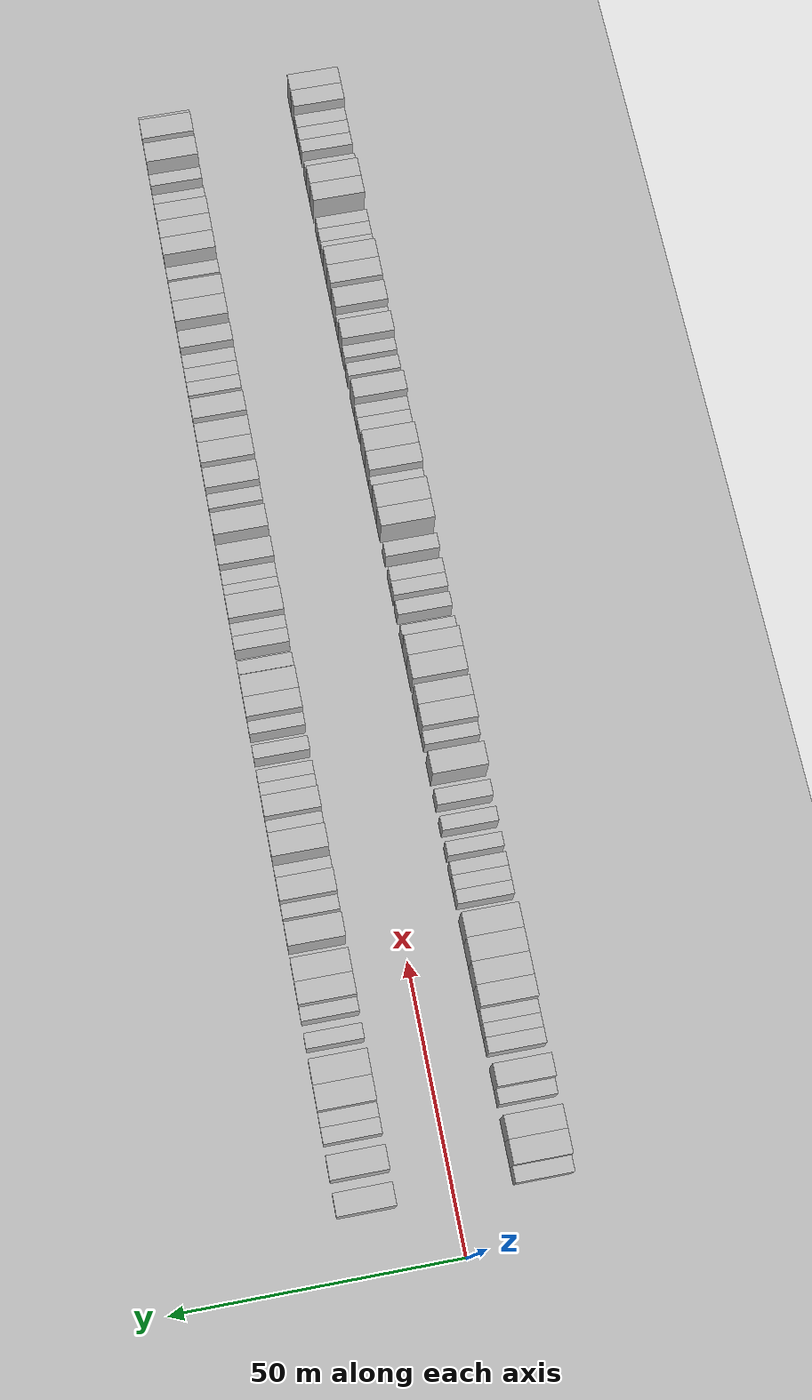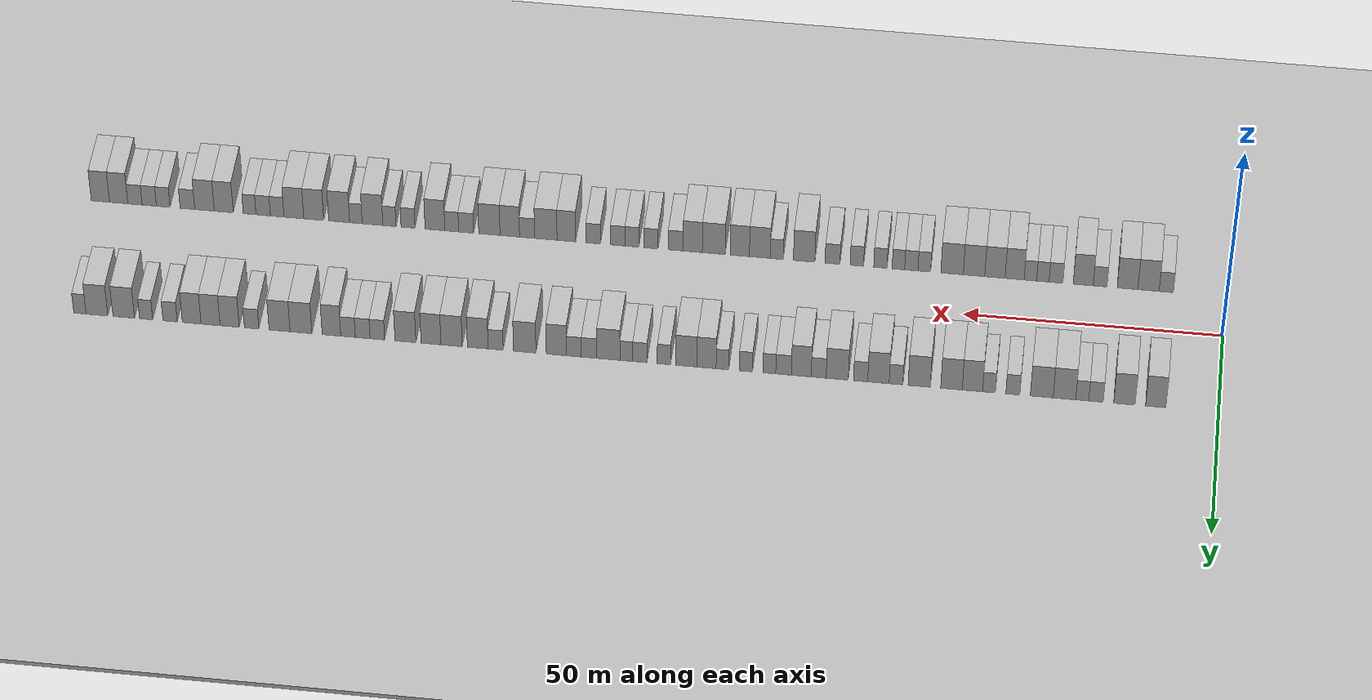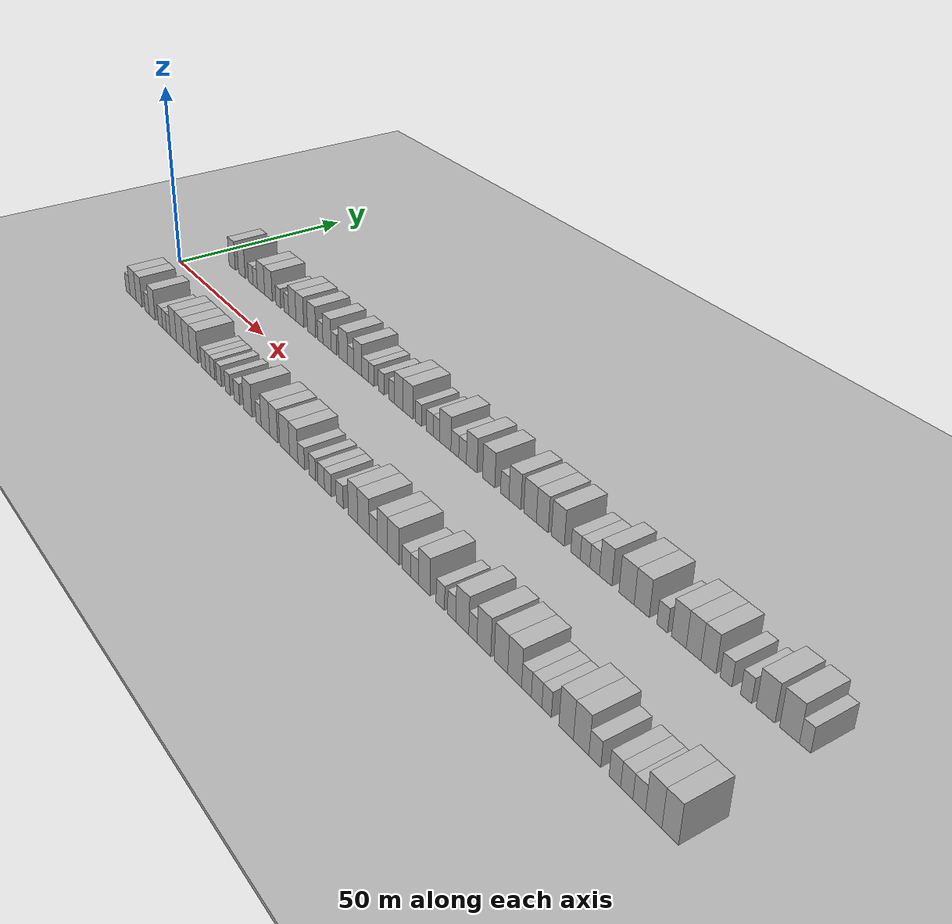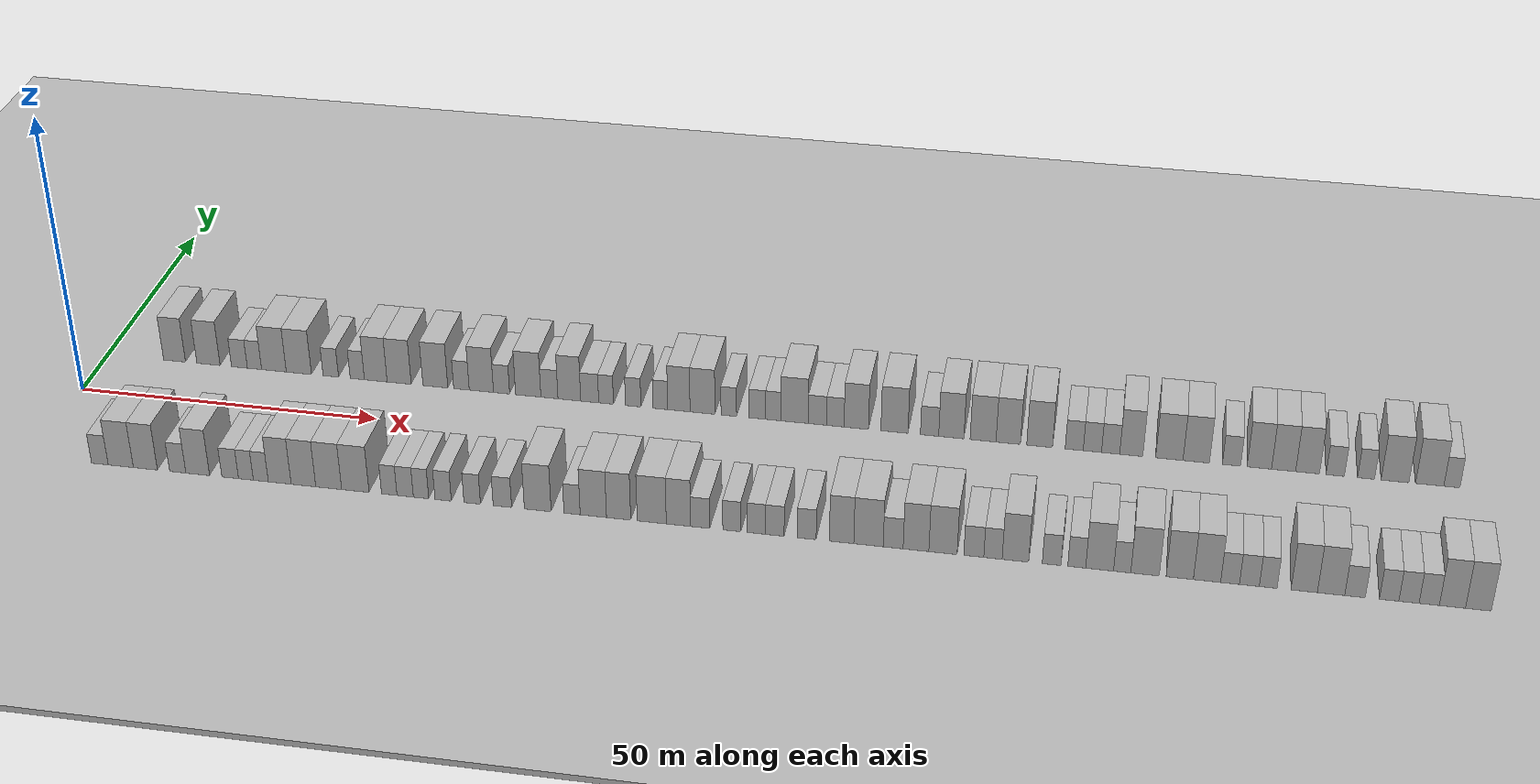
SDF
<?xml version="1.0" encoding="utf-8"?>

<sdf version="1.6">

   <world name="default">

      <gui fullscreen="0">

         <camera name="user_camera">

            <pose>-15 0 4.57585 0 0 0</pose>

            <view_controller>orbit</view_controller>

         </camera>

      </gui>

      <scene>

         <sky>

           <clouds>

             <speed>12</speed>

           </clouds>

         </sky>

         <ambient>0.4 0.4 0.4 1</ambient>

         <background>0.7 0.7 0.7 1</background>

         <shadows>1</shadows>

      </scene>

      <gravity>0 0 -9.8066</gravity>

      <magnetic_field>6e-06 2.3e-05 -4.2e-05</magnetic_field>

      <physics default="0" name="default_physics" type="ode">

         <ode>

            <solver>

               <type>quick</type>

               <iters>10</iters>

               <sor>1.0</sor>

               <use_dynamic_moi_rescaling>0</use_dynamic_moi_rescaling>

            </solver>

            <constraints>

               <cfm>0</cfm>

               <erp>0.2</erp>

               <contact_max_correcting_vel>100</contact_max_correcting_vel>

               <contact_surface_layer>0.001</contact_surface_layer>

            </constraints>

         </ode>

         <max_step_size>0.004</max_step_size>

         <real_time_factor>1</real_time_factor>

         <real_time_update_rate>250</real_time_update_rate>

      </physics>

      <light name="sun" type="directional">

         <cast_shadows>1</cast_shadows>

         <pose>0 0 10 0 0 0</pose>

         <diffuse>0.8 0.8 0.8 1</diffuse>

         <specular>0.2 0.2 0.2 1</specular>

         <attenuation>

            <range>1000</range>

            <constant>0.9</constant>

            <linear>0.01</linear>

            <quadratic>0.001</quadratic>

         </attenuation>

         <direction>-0.5 0.1 -0.9</direction>

      </light>

      <include>

         <name>ground_plane_1</name>

         <uri>model://HANNAS_ground_plane</uri>

         <pose>0 0 0  0 0 0</pose>

      </include>

      <include>

         <name>ground_plane_2</name>

         <uri>model://HANNAS_ground_plane</uri>

         <pose>100 0 0  0 0 0</pose>

      </include>

      <model name="building_1">

         <static>1</static>

         <pose frame="">11.9177 15.0000 0 0.000000 0.000000 1.570796</pose>

         <link name="link">

            <pose frame="">0 0 4.50 0 0 0</pose>

            <collision name="collision">

               <geometry>

                  <box>

                     <size>10.0000 3.8354 9.0000</size>

                  </box>

               </geometry>

               <max_contacts>10</max_contacts>

               <surface>

                  <contact>

                     <ode/>

                  </contact>

                  <bounce/>

                  <friction>

                     <torsional>

                        <ode/>

                     </torsional>

                     <ode/>

                  </friction>

               </surface>

            </collision>

            <visual name="visual">

               <cast_shadows>0</cast_shadows>

               <geometry>

                  <box>

                     <size>10.0000 3.8354 9.0000</size>

                  </box>

               </geometry>

               <material>

                  <script>

                     <uri>model://HANNAS_wall/materials/scripts</uri>

                     <uri>model://HANNAS_wall/materials/textures</uri>

                     <name>vrc/HANNAS_wall</name>

                  </script>

               </material>

            </visual>

            <self_collide>0</self_collide>

            <enable_wind>0</enable_wind>

            <kinematic>0</kinematic>

         </link>

      </model>

      <model name="building_2">

         <static>1</static>

         <pose frame="">17.8606 15.0000 0 0.000000 0.000000 1.570796</pose>

         <link name="link">

            <pose frame="">0 0 4.50 0 0 0</pose>

            <collision name="collision">

               <geometry>

                  <box>

                     <size>10.0000 4.0505 9.0000</size>

                  </box>

               </geometry>

               <max_contacts>10</max_contacts>

               <surface>

                  <contact>

                     <ode/>

                  </contact>

                  <bounce/>

                  <friction>

                     <torsional>

                        <ode/>

                     </torsional>

                     <ode/>

                  </friction>

               </surface>

            </collision>

            <visual name="visual">

               <cast_shadows>0</cast_shadows>

               <geometry>

                  <box>

                     <size>10.0000 4.0505 9.0000</size>

                  </box>

               </geometry>

               <material>

                  <script>

                     <uri>model://HANNAS_wall/materials/scripts</uri>

                     <uri>model://HANNAS_wall/materials/textures</uri>

                     <name>vrc/HANNAS_wall</name>

                  </script>

               </material>

            </visual>

            <self_collide>0</self_collide>

            <enable_wind>0</enable_wind>

            <kinematic>0</kinematic>

         </link>

      </model>

      <model name="building_3">

         <static>1</static>

         <pose frame="">23.2606 15.0000 0 0.000000 0.000000 1.570796</pose>

         <link name="link">

            <pose frame="">0 0 3.00 0 0 0</pose>

            <collision name="collision">

               <geometry>

                  <box>

                     <size>10.0000 2.7494 6.0000</size>

                  </box>

               </geometry>

               <max_contacts>10</max_contacts>

               <surface>

                  <contact>

                     <ode/>

                  </contact>

                  <bounce/>

                  <friction>

                     <torsional>

                        <ode/>

                     </torsional>

                     <ode/>

                  </friction>

               </surface>

            </collision>

            <visual name="visual">

               <cast_shadows>0</cast_shadows>

               <geometry>

                  <box>

                     <size>10.0000 2.7494 6.0000</size>

                  </box>

               </geometry>

               <material>

                  <script>

                     <uri>model://HANNAS_wall/materials/scripts</uri>

                     <uri>model://HANNAS_wall/materials/textures</uri>

                     <name>vrc/HANNAS_wall</name>

                  </script>

               </material>

            </visual>

            <self_collide>0</self_collide>

            <enable_wind>0</enable_wind>

            <kinematic>0</kinematic>

         </link>

      </model>

      <model name="building_4">

         <static>1</static>

         <pose frame="">25.8726 15.0000 0 0.000000 0.000000 1.570796</pose>

         <link name="link">

            <pose frame="">0 0 3.00 0 0 0</pose>

            <collision name="collision">

               <geometry>

                  <box>

                     <size>10.0000 2.4745 6.0000</size>

                  </box>

               </geometry>

               <max_contacts>10</max_contacts>

               <surface>

                  <contact>

                     <ode/>

                  </contact>

                  <bounce/>

                  <friction>

                     <torsional>

                        <ode/>

                     </torsional>

                     <ode/>

                  </friction>

               </surface>

            </collision>

            <visual name="visual">

               <cast_shadows>0</cast_shadows>

               <geometry>

                  <box>

                     <size>10.0000 2.4745 6.0000</size>

                  </box>

               </geometry>

               <material>

                  <script>

                     <uri>model://HANNAS_wall/materials/scripts</uri>

                     <uri>model://HANNAS_wall/materials/textures</uri>

                     <name>vrc/HANNAS_wall</name>

                  </script>

               </material>

            </visual>

            <self_collide>0</self_collide>

            <enable_wind>0</enable_wind>

            <kinematic>0</kinematic>

         </link>

      </model>

      <model name="building_5">

         <static>1</static>

         <pose frame="">29.2532 15.0000 0 0.000000 0.000000 1.570796</pose>

         <link name="link">

            <pose frame="">0 0 4.50 0 0 0</pose>

            <collision name="collision">

               <geometry>

                  <box>

                     <size>10.0000 4.2869 9.0000</size>

                  </box>

               </geometry>

               <max_contacts>10</max_contacts>

               <surface>

                  <contact>

                     <ode/>

                  </contact>

                  <bounce/>

                  <friction>

                     <torsional>

                        <ode/>

                     </torsional>

                     <ode/>

                  </friction>

               </surface>

            </collision>

            <visual name="visual">

               <cast_shadows>0</cast_shadows>

               <geometry>

                  <box>

                     <size>10.0000 4.2869 9.0000</size>

                  </box>

               </geometry>

               <material>

                  <script>

                     <uri>model://HANNAS_wall/materials/scripts</uri>

                     <uri>model://HANNAS_wall/materials/textures</uri>

                     <name>vrc/HANNAS_wall</name>

                  </script>

               </material>

            </visual>

            <self_collide>0</self_collide>

            <enable_wind>0</enable_wind>

            <kinematic>0</kinematic>

         </link>

      </model>

      <model name="building_6">

         <static>1</static>

         <pose frame="">33.5742 15.0000 0 0.000000 0.000000 1.570796</pose>

         <link name="link">

            <pose frame="">0 0 4.50 0 0 0</pose>

            <collision name="collision">

               <geometry>

                  <box>

                     <size>10.0000 4.3551 9.0000</size>

                  </box>

               </geometry>

               <max_contacts>10</max_contacts>

               <surface>

                  <contact>

                     <ode/>

                  </contact>

                  <bounce/>

                  <friction>

                     <torsional>

                        <ode/>

                     </torsional>

                     <ode/>

                  </friction>

               </surface>

            </collision>

            <visual name="visual">

               <cast_shadows>0</cast_shadows>

               <geometry>

                  <box>

                     <size>10.0000 4.3551 9.0000</size>

                  </box>

               </geometry>

               <material>

                  <script>

                     <uri>model://HANNAS_wall/materials/scripts</uri>

                     <uri>model://HANNAS_wall/materials/textures</uri>

                     <name>vrc/HANNAS_wall</name>

                  </script>

               </material>

            </visual>

            <self_collide>0</self_collide>

            <enable_wind>0</enable_wind>

            <kinematic>0</kinematic>

         </link>

      </model>

      <model name="building_7">

         <static>1</static>

         <pose frame="">39.0809 15.0000 0 0.000000 0.000000 1.570796</pose>

         <link name="link">

            <pose frame="">0 0 3.00 0 0 0</pose>

            <collision name="collision">

               <geometry>

                  <box>

                     <size>10.0000 2.6583 6.0000</size>

                  </box>

               </geometry>

               <max_contacts>10</max_contacts>

               <surface>

                  <contact>

                     <ode/>

                  </contact>

                  <bounce/>

                  <friction>

                     <torsional>

                        <ode/>

                     </torsional>

                     <ode/>

                  </friction>

               </surface>

            </collision>

            <visual name="visual">

               <cast_shadows>0</cast_shadows>

               <geometry>

                  <box>

                     <size>10.0000 2.6583 6.0000</size>

                  </box>

               </geometry>

               <material>

                  <script>

                     <uri>model://HANNAS_wall/materials/scripts</uri>

                     <uri>model://HANNAS_wall/materials/textures</uri>

                     <name>vrc/HANNAS_wall</name>

                  </script>

               </material>

            </visual>

            <self_collide>0</self_collide>

            <enable_wind>0</enable_wind>

            <kinematic>0</kinematic>

         </link>

      </model>

      <model name="building_8">

         <static>1</static>

         <pose frame="">43.6283 15.0000 0 0.000000 0.000000 1.570796</pose>

         <link name="link">

            <pose frame="">0 0 3.00 0 0 0</pose>

            <collision name="collision">

               <geometry>

                  <box>

                     <size>10.0000 2.4365 6.0000</size>

                  </box>

               </geometry>

               <max_contacts>10</max_contacts>

               <surface>

                  <contact>

                     <ode/>

                  </contact>

                  <bounce/>

                  <friction>

                     <torsional>

                        <ode/>

                     </torsional>

                     <ode/>

                  </friction>

               </surface>

            </collision>

            <visual name="visual">

               <cast_shadows>0</cast_shadows>

               <geometry>

                  <box>

                     <size>10.0000 2.4365 6.0000</size>

                  </box>

               </geometry>

               <material>

                  <script>

                     <uri>model://HANNAS_wall/materials/scripts</uri>

                     <uri>model://HANNAS_wall/materials/textures</uri>

                     <name>vrc/HANNAS_wall</name>

                  </script>

               </material>

            </visual>

            <self_collide>0</self_collide>

            <enable_wind>0</enable_wind>

            <kinematic>0</kinematic>

         </link>

      </model>

      <model name="building_9">

         <static>1</static>

         <pose frame="">46.7933 15.0000 0 0.000000 0.000000 1.570796</pose>

         <link name="link">

            <pose frame="">0 0 4.50 0 0 0</pose>

            <collision name="collision">

               <geometry>

                  <box>

                     <size>10.0000 3.8934 9.0000</size>

                  </box>

               </geometry>

               <max_contacts>10</max_contacts>

               <surface>

                  <contact>

                     <ode/>

                  </contact>

                  <bounce/>

                  <friction>

                     <torsional>

                        <ode/>

                     </torsional>

                     <ode/>

                  </friction>

               </surface>

            </collision>

            <visual name="visual">

               <cast_shadows>0</cast_shadows>

               <geometry>

                  <box>

                     <size>10.0000 3.8934 9.0000</size>

                  </box>

               </geometry>

               <material>

                  <script>

                     <uri>model://HANNAS_wall/materials/scripts</uri>

                     <uri>model://HANNAS_wall/materials/textures</uri>

                     <name>vrc/HANNAS_wall</name>

                  </script>

               </material>

            </visual>

            <self_collide>0</self_collide>

            <enable_wind>0</enable_wind>

            <kinematic>0</kinematic>

         </link>

      </model>

      <model name="building_10">

         <static>1</static>

         <pose frame="">50.7917 15.0000 0 0.000000 0.000000 1.570796</pose>

         <link name="link">

            <pose frame="">0 0 4.50 0 0 0</pose>

            <collision name="collision">

               <geometry>

                  <box>

                     <size>10.0000 4.1034 9.0000</size>

                  </box>

               </geometry>

               <max_contacts>10</max_contacts>

               <surface>

                  <contact>

                     <ode/>

                  </contact>

                  <bounce/>

                  <friction>

                     <torsional>

                        <ode/>

                     </torsional>

                     <ode/>

                  </friction>

               </surface>

            </collision>

            <visual name="visual">

               <cast_shadows>0</cast_shadows>

               <geometry>

                  <box>

                     <size>10.0000 4.1034 9.0000</size>

                  </box>

               </geometry>

               <material>

                  <script>

                     <uri>model://HANNAS_wall/materials/scripts</uri>

                     <uri>model://HANNAS_wall/materials/textures</uri>

                     <name>vrc/HANNAS_wall</name>

                  </script>

               </material>

            </visual>

            <self_collide>0</self_collide>

            <enable_wind>0</enable_wind>

            <kinematic>0</kinematic>

         </link>

      </model>

      <model name="building_11">

         <static>1</static>

         <pose frame="">56.9560 15.0000 0 0.000000 0.000000 1.570796</pose>

         <link name="link">

            <pose frame="">0 0 4.50 0 0 0</pose>

            <collision name="collision">

               <geometry>

                  <box>

                     <size>10.0000 4.2253 9.0000</size>

                  </box>

               </geometry>

               <max_contacts>10</max_contacts>

               <surface>

                  <contact>

                     <ode/>

                  </contact>

                  <bounce/>

                  <friction>

                     <torsional>

                        <ode/>

                     </torsional>

                     <ode/>

                  </friction>

               </surface>

            </collision>

            <visual name="visual">

               <cast_shadows>0</cast_shadows>

               <geometry>

                  <box>

                     <size>10.0000 4.2253 9.0000</size>

                  </box>

               </geometry>

               <material>

                  <script>

                     <uri>model://HANNAS_wall/materials/scripts</uri>

                     <uri>model://HANNAS_wall/materials/textures</uri>

                     <name>vrc/HANNAS_wall</name>

                  </script>

               </material>

            </visual>

            <self_collide>0</self_collide>

            <enable_wind>0</enable_wind>

            <kinematic>0</kinematic>

         </link>

      </model>

      <model name="building_12">

         <static>1</static>

         <pose frame="">61.3837 15.0000 0 0.000000 0.000000 1.570796</pose>

         <link name="link">

            <pose frame="">0 0 3.00 0 0 0</pose>

            <collision name="collision">

               <geometry>

                  <box>

                     <size>10.0000 2.6300 6.0000</size>

                  </box>

               </geometry>

               <max_contacts>10</max_contacts>

               <surface>

                  <contact>

                     <ode/>

                  </contact>

                  <bounce/>

                  <friction>

                     <torsional>

                        <ode/>

                     </torsional>

                     <ode/>

                  </friction>

               </surface>

            </collision>

            <visual name="visual">

               <cast_shadows>0</cast_shadows>

               <geometry>

                  <box>

                     <size>10.0000 2.6300 6.0000</size>

                  </box>

               </geometry>

               <material>

                  <script>

                     <uri>model://HANNAS_wall/materials/scripts</uri>

                     <uri>model://HANNAS_wall/materials/textures</uri>

                     <name>vrc/HANNAS_wall</name>

                  </script>

               </material>

            </visual>

            <self_collide>0</self_collide>

            <enable_wind>0</enable_wind>

            <kinematic>0</kinematic>

         </link>

      </model>

      <model name="building_13">

         <static>1</static>

         <pose frame="">64.7471 15.0000 0 0.000000 0.000000 1.570796</pose>

         <link name="link">

            <pose frame="">0 0 4.50 0 0 0</pose>

            <collision name="collision">

               <geometry>

                  <box>

                     <size>10.0000 4.0969 9.0000</size>

                  </box>

               </geometry>

               <max_contacts>10</max_contacts>

               <surface>

                  <contact>

                     <ode/>

                  </contact>

                  <bounce/>

                  <friction>

                     <torsional>

                        <ode/>

                     </torsional>

                     <ode/>

                  </friction>

               </surface>

            </collision>

            <visual name="visual">

               <cast_shadows>0</cast_shadows>

               <geometry>

                  <box>

                     <size>10.0000 4.0969 9.0000</size>

                  </box>

               </geometry>

               <material>

                  <script>

                     <uri>model://HANNAS_wall/materials/scripts</uri>

                     <uri>model://HANNAS_wall/materials/textures</uri>

                     <name>vrc/HANNAS_wall</name>

                  </script>

               </material>

            </visual>

            <self_collide>0</self_collide>

            <enable_wind>0</enable_wind>

            <kinematic>0</kinematic>

         </link>

      </model>

      <model name="building_14">

         <static>1</static>

         <pose frame="">68.1561 15.0000 0 0.000000 0.000000 1.570796</pose>

         <link name="link">

            <pose frame="">0 0 3.00 0 0 0</pose>

            <collision name="collision">

               <geometry>

                  <box>

                     <size>10.0000 2.7211 6.0000</size>

                  </box>

               </geometry>

               <max_contacts>10</max_contacts>

               <surface>

                  <contact>

                     <ode/>

                  </contact>

                  <bounce/>

                  <friction>

                     <torsional>

                        <ode/>

                     </torsional>

                     <ode/>

                  </friction>

               </surface>

            </collision>

            <visual name="visual">

               <cast_shadows>0</cast_shadows>

               <geometry>

                  <box>

                     <size>10.0000 2.7211 6.0000</size>

                  </box>

               </geometry>

               <material>

                  <script>

                     <uri>model://HANNAS_wall/materials/scripts</uri>

                     <uri>model://HANNAS_wall/materials/textures</uri>

                     <name>vrc/HANNAS_wall</name>

                  </script>

               </material>

            </visual>

            <self_collide>0</self_collide>

            <enable_wind>0</enable_wind>

            <kinematic>0</kinematic>

         </link>

      </model>

      <model name="building_15">

         <static>1</static>

         <pose frame="">72.6376 15.0000 0 0.000000 0.000000 1.570796</pose>

         <link name="link">

            <pose frame="">0 0 4.50 0 0 0</pose>

            <collision name="collision">

               <geometry>

                  <box>

                     <size>10.0000 4.2419 9.0000</size>

                  </box>

               </geometry>

               <max_contacts>10</max_contacts>

               <surface>

                  <contact>

                     <ode/>

                  </contact>

                  <bounce/>

                  <friction>

                     <torsional>

                        <ode/>

                     </torsional>

                     <ode/>

                  </friction>

               </surface>

            </collision>

            <visual name="visual">

               <cast_shadows>0</cast_shadows>

               <geometry>

                  <box>

                     <size>10.0000 4.2419 9.0000</size>

                  </box>

               </geometry>

               <material>

                  <script>

                     <uri>model://HANNAS_wall/materials/scripts</uri>

                     <uri>model://HANNAS_wall/materials/textures</uri>

                     <name>vrc/HANNAS_wall</name>

                  </script>

               </material>

            </visual>

            <self_collide>0</self_collide>

            <enable_wind>0</enable_wind>

            <kinematic>0</kinematic>

         </link>

      </model>

      <model name="building_16">

         <static>1</static>

         <pose frame="">76.1897 15.0000 0 0.000000 0.000000 1.570796</pose>

         <link name="link">

            <pose frame="">0 0 3.00 0 0 0</pose>

            <collision name="collision">

               <geometry>

                  <box>

                     <size>10.0000 2.8624 6.0000</size>

                  </box>

               </geometry>

               <max_contacts>10</max_contacts>

               <surface>

                  <contact>

                     <ode/>

                  </contact>

                  <bounce/>

                  <friction>

                     <torsional>

                        <ode/>

                     </torsional>

                     <ode/>

                  </friction>

               </surface>

            </collision>

            <visual name="visual">

               <cast_shadows>0</cast_shadows>

               <geometry>

                  <box>

                     <size>10.0000 2.8624 6.0000</size>

                  </box>

               </geometry>

               <material>

                  <script>

                     <uri>model://HANNAS_wall/materials/scripts</uri>

                     <uri>model://HANNAS_wall/materials/textures</uri>

                     <name>vrc/HANNAS_wall</name>

                  </script>

               </material>

            </visual>

            <self_collide>0</self_collide>

            <enable_wind>0</enable_wind>

            <kinematic>0</kinematic>

         </link>

      </model>

      <model name="building_17">

         <static>1</static>

         <pose frame="">79.5258 15.0000 0 0.000000 0.000000 1.570796</pose>

         <link name="link">

            <pose frame="">0 0 4.50 0 0 0</pose>

            <collision name="collision">

               <geometry>

                  <box>

                     <size>10.0000 3.8097 9.0000</size>

                  </box>

               </geometry>

               <max_contacts>10</max_contacts>

               <surface>

                  <contact>

                     <ode/>

                  </contact>

                  <bounce/>

                  <friction>

                     <torsional>

                        <ode/>

                     </torsional>

                     <ode/>

                  </friction>

               </surface>

            </collision>

            <visual name="visual">

               <cast_shadows>0</cast_shadows>

               <geometry>

                  <box>

                     <size>10.0000 3.8097 9.0000</size>

                  </box>

               </geometry>

               <material>

                  <script>

                     <uri>model://HANNAS_wall/materials/scripts</uri>

                     <uri>model://HANNAS_wall/materials/textures</uri>

                     <name>vrc/HANNAS_wall</name>

                  </script>

               </material>

            </visual>

            <self_collide>0</self_collide>

            <enable_wind>0</enable_wind>

            <kinematic>0</kinematic>

         </link>

      </model>

      <model name="building_18">

         <static>1</static>

         <pose frame="">82.9254 15.0000 0 0.000000 0.000000 1.570796</pose>

         <link name="link">

            <pose frame="">0 0 3.00 0 0 0</pose>

            <collision name="collision">

               <geometry>

                  <box>

                     <size>10.0000 2.9894 6.0000</size>

                  </box>

               </geometry>

               <max_contacts>10</max_contacts>

               <surface>

                  <contact>

                     <ode/>

                  </contact>

                  <bounce/>

                  <friction>

                     <torsional>

                        <ode/>

                     </torsional>

                     <ode/>

                  </friction>

               </surface>

            </collision>

            <visual name="visual">

               <cast_shadows>0</cast_shadows>

               <geometry>

                  <box>

                     <size>10.0000 2.9894 6.0000</size>

                  </box>

               </geometry>

               <material>

                  <script>

                     <uri>model://HANNAS_wall/materials/scripts</uri>

                     <uri>model://HANNAS_wall/materials/textures</uri>

                     <name>vrc/HANNAS_wall</name>

                  </script>

               </material>

            </visual>

            <self_collide>0</self_collide>

            <enable_wind>0</enable_wind>

            <kinematic>0</kinematic>

         </link>

      </model>

      <model name="building_19">

         <static>1</static>

         <pose frame="">85.6485 15.0000 0 0.000000 0.000000 1.570796</pose>

         <link name="link">

            <pose frame="">0 0 3.00 0 0 0</pose>

            <collision name="collision">

               <geometry>

                  <box>

                     <size>10.0000 2.4570 6.0000</size>

                  </box>

               </geometry>

               <max_contacts>10</max_contacts>

               <surface>

                  <contact>

                     <ode/>

                  </contact>

                  <bounce/>

                  <friction>

                     <torsional>

                        <ode/>

                     </torsional>

                     <ode/>

                  </friction>

               </surface>

            </collision>

            <visual name="visual">

               <cast_shadows>0</cast_shadows>

               <geometry>

                  <box>

                     <size>10.0000 2.4570 6.0000</size>

                  </box>

               </geometry>

               <material>

                  <script>

                     <uri>model://HANNAS_wall/materials/scripts</uri>

                     <uri>model://HANNAS_wall/materials/textures</uri>

                     <name>vrc/HANNAS_wall</name>

                  </script>

               </material>

            </visual>

            <self_collide>0</self_collide>

            <enable_wind>0</enable_wind>

            <kinematic>0</kinematic>

         </link>

      </model>

      <model name="building_20">

         <static>1</static>

         <pose frame="">90.1554 15.0000 0 0.000000 0.000000 1.570796</pose>

         <link name="link">

            <pose frame="">0 0 3.00 0 0 0</pose>

            <collision name="collision">

               <geometry>

                  <box>

                     <size>10.0000 2.5568 6.0000</size>

                  </box>

               </geometry>

               <max_contacts>10</max_contacts>

               <surface>

                  <contact>

                     <ode/>

                  </contact>

                  <bounce/>

                  <friction>

                     <torsional>

                        <ode/>

                     </torsional>

                     <ode/>

                  </friction>

               </surface>

            </collision>

            <visual name="visual">

               <cast_shadows>0</cast_shadows>

               <geometry>

                  <box>

                     <size>10.0000 2.5568 6.0000</size>

                  </box>

               </geometry>

               <material>

                  <script>

                     <uri>model://HANNAS_wall/materials/scripts</uri>

                     <uri>model://HANNAS_wall/materials/textures</uri>

                     <name>vrc/HANNAS_wall</name>

                  </script>

               </material>

            </visual>

            <self_collide>0</self_collide>

            <enable_wind>0</enable_wind>

            <kinematic>0</kinematic>

         </link>

      </model>

      <model name="building_21">

         <static>1</static>

         <pose frame="">94.6502 15.0000 0 0.000000 0.000000 1.570796</pose>

         <link name="link">

            <pose frame="">0 0 3.00 0 0 0</pose>

            <collision name="collision">

               <geometry>

                  <box>

                     <size>10.0000 2.4329 6.0000</size>

                  </box>

               </geometry>

               <max_contacts>10</max_contacts>

               <surface>

                  <contact>

                     <ode/>

                  </contact>

                  <bounce/>

                  <friction>

                     <torsional>

                        <ode/>

                     </torsional>

                     <ode/>

                  </friction>

               </surface>

            </collision>

            <visual name="visual">

               <cast_shadows>0</cast_shadows>

               <geometry>

                  <box>

                     <size>10.0000 2.4329 6.0000</size>

                  </box>

               </geometry>

               <material>

                  <script>

                     <uri>model://HANNAS_wall/materials/scripts</uri>

                     <uri>model://HANNAS_wall/materials/textures</uri>

                     <name>vrc/HANNAS_wall</name>

                  </script>

               </material>

            </visual>

            <self_collide>0</self_collide>

            <enable_wind>0</enable_wind>

            <kinematic>0</kinematic>

         </link>

      </model>

      <model name="building_22">

         <static>1</static>

         <pose frame="">97.7045 15.0000 0 0.000000 0.000000 1.570796</pose>

         <link name="link">

            <pose frame="">0 0 4.50 0 0 0</pose>

            <collision name="collision">

               <geometry>

                  <box>

                     <size>10.0000 3.6756 9.0000</size>

                  </box>

               </geometry>

               <max_contacts>10</max_contacts>

               <surface>

                  <contact>

                     <ode/>

                  </contact>

                  <bounce/>

                  <friction>

                     <torsional>

                        <ode/>

                     </torsional>

                     <ode/>

                  </friction>

               </surface>

            </collision>

            <visual name="visual">

               <cast_shadows>0</cast_shadows>

               <geometry>

                  <box>

                     <size>10.0000 3.6756 9.0000</size>

                  </box>

               </geometry>

               <material>

                  <script>

                     <uri>model://HANNAS_wall/materials/scripts</uri>

                     <uri>model://HANNAS_wall/materials/textures</uri>

                     <name>vrc/HANNAS_wall</name>

                  </script>

               </material>

            </visual>

            <self_collide>0</self_collide>

            <enable_wind>0</enable_wind>

            <kinematic>0</kinematic>

         </link>

      </model>

      <model name="building_23">

         <static>1</static>

         <pose frame="">101.5891 15.0000 0 0.000000 0.000000 1.570796</pose>

         <link name="link">

            <pose frame="">0 0 4.50 0 0 0</pose>

            <collision name="collision">

               <geometry>

                  <box>

                     <size>10.0000 4.0937 9.0000</size>

                  </box>

               </geometry>

               <max_contacts>10</max_contacts>

               <surface>

                  <contact>

                     <ode/>

                  </contact>

                  <bounce/>

                  <friction>

                     <torsional>

                        <ode/>

                     </torsional>

                     <ode/>

                  </friction>

               </surface>

            </collision>

            <visual name="visual">

               <cast_shadows>0</cast_shadows>

               <geometry>

                  <box>

                     <size>10.0000 4.0937 9.0000</size>

                  </box>

               </geometry>

               <material>

                  <script>

                     <uri>model://HANNAS_wall/materials/scripts</uri>

                     <uri>model://HANNAS_wall/materials/textures</uri>

                     <name>vrc/HANNAS_wall</name>

                  </script>

               </material>

            </visual>

            <self_collide>0</self_collide>

            <enable_wind>0</enable_wind>

            <kinematic>0</kinematic>

         </link>

      </model>

      <model name="building_24">

         <static>1</static>

         <pose frame="">105.9074 15.0000 0 0.000000 0.000000 1.570796</pose>

         <link name="link">

            <pose frame="">0 0 3.00 0 0 0</pose>

            <collision name="collision">

               <geometry>

                  <box>

                     <size>10.0000 2.5429 6.0000</size>

                  </box>

               </geometry>

               <max_contacts>10</max_contacts>

               <surface>

                  <contact>

                     <ode/>

                  </contact>

                  <bounce/>

                  <friction>

                     <torsional>

                        <ode/>

                     </torsional>

                     <ode/>

                  </friction>

               </surface>

            </collision>

            <visual name="visual">

               <cast_shadows>0</cast_shadows>

               <geometry>

                  <box>

                     <size>10.0000 2.5429 6.0000</size>

                  </box>

               </geometry>

               <material>

                  <script>

                     <uri>model://HANNAS_wall/materials/scripts</uri>

                     <uri>model://HANNAS_wall/materials/textures</uri>

                     <name>vrc/HANNAS_wall</name>

                  </script>

               </material>

            </visual>

            <self_collide>0</self_collide>

            <enable_wind>0</enable_wind>

            <kinematic>0</kinematic>

         </link>

      </model>

      <model name="building_25">

         <static>1</static>

         <pose frame="">110.5502 15.0000 0 0.000000 0.000000 1.570796</pose>

         <link name="link">

            <pose frame="">0 0 3.00 0 0 0</pose>

            <collision name="collision">

               <geometry>

                  <box>

                     <size>10.0000 2.7427 6.0000</size>

                  </box>

               </geometry>

               <max_contacts>10</max_contacts>

               <surface>

                  <contact>

                     <ode/>

                  </contact>

                  <bounce/>

                  <friction>

                     <torsional>

                        <ode/>

                     </torsional>

                     <ode/>

                  </friction>

               </surface>

            </collision>

            <visual name="visual">

               <cast_shadows>0</cast_shadows>

               <geometry>

                  <box>

                     <size>10.0000 2.7427 6.0000</size>

                  </box>

               </geometry>

               <material>

                  <script>

                     <uri>model://HANNAS_wall/materials/scripts</uri>

                     <uri>model://HANNAS_wall/materials/textures</uri>

                     <name>vrc/HANNAS_wall</name>

                  </script>

               </material>

            </visual>

            <self_collide>0</self_collide>

            <enable_wind>0</enable_wind>

            <kinematic>0</kinematic>

         </link>

      </model>

      <model name="building_26">

         <static>1</static>

         <pose frame="">113.1542 15.0000 0 0.000000 0.000000 1.570796</pose>

         <link name="link">

            <pose frame="">0 0 3.00 0 0 0</pose>

            <collision name="collision">

               <geometry>

                  <box>

                     <size>10.0000 2.4653 6.0000</size>

                  </box>

               </geometry>

               <max_contacts>10</max_contacts>

               <surface>

                  <contact>

                     <ode/>

                  </contact>

                  <bounce/>

                  <friction>

                     <torsional>

                        <ode/>

                     </torsional>

                     <ode/>

                  </friction>

               </surface>

            </collision>

            <visual name="visual">

               <cast_shadows>0</cast_shadows>

               <geometry>

                  <box>

                     <size>10.0000 2.4653 6.0000</size>

                  </box>

               </geometry>

               <material>

                  <script>

                     <uri>model://HANNAS_wall/materials/scripts</uri>

                     <uri>model://HANNAS_wall/materials/textures</uri>

                     <name>vrc/HANNAS_wall</name>

                  </script>

               </material>

            </visual>

            <self_collide>0</self_collide>

            <enable_wind>0</enable_wind>

            <kinematic>0</kinematic>

         </link>

      </model>

      <model name="building_27">

         <static>1</static>

         <pose frame="">116.6124 15.0000 0 0.000000 0.000000 1.570796</pose>

         <link name="link">

            <pose frame="">0 0 4.50 0 0 0</pose>

            <collision name="collision">

               <geometry>

                  <box>

                     <size>10.0000 4.4511 9.0000</size>

                  </box>

               </geometry>

               <max_contacts>10</max_contacts>

               <surface>

                  <contact>

                     <ode/>

                  </contact>

                  <bounce/>

                  <friction>

                     <torsional>

                        <ode/>

                     </torsional>

                     <ode/>

                  </friction>

               </surface>

            </collision>

            <visual name="visual">

               <cast_shadows>0</cast_shadows>

               <geometry>

                  <box>

                     <size>10.0000 4.4511 9.0000</size>

                  </box>

               </geometry>

               <material>

                  <script>

                     <uri>model://HANNAS_wall/materials/scripts</uri>

                     <uri>model://HANNAS_wall/materials/textures</uri>

                     <name>vrc/HANNAS_wall</name>

                  </script>

               </material>

            </visual>

            <self_collide>0</self_collide>

            <enable_wind>0</enable_wind>

            <kinematic>0</kinematic>

         </link>

      </model>

      <model name="building_28">

         <static>1</static>

         <pose frame="">120.3287 15.0000 0 0.000000 0.000000 1.570796</pose>

         <link name="link">

            <pose frame="">0 0 3.00 0 0 0</pose>

            <collision name="collision">

               <geometry>

                  <box>

                     <size>10.0000 2.9816 6.0000</size>

                  </box>

               </geometry>

               <max_contacts>10</max_contacts>

               <surface>

                  <contact>

                     <ode/>

                  </contact>

                  <bounce/>

                  <friction>

                     <torsional>

                        <ode/>

                     </torsional>

                     <ode/>

                  </friction>

               </surface>

            </collision>

            <visual name="visual">

               <cast_shadows>0</cast_shadows>

               <geometry>

                  <box>

                     <size>10.0000 2.9816 6.0000</size>

                  </box>

               </geometry>

               <material>

                  <script>

                     <uri>model://HANNAS_wall/materials/scripts</uri>

                     <uri>model://HANNAS_wall/materials/textures</uri>

                     <name>vrc/HANNAS_wall</name>

                  </script>

               </material>

            </visual>

            <self_collide>0</self_collide>

            <enable_wind>0</enable_wind>

            <kinematic>0</kinematic>

         </link>

      </model>

      <model name="building_29">

         <static>1</static>

         <pose frame="">123.2428 15.0000 0 0.000000 0.000000 1.570796</pose>

         <link name="link">

            <pose frame="">0 0 3.00 0 0 0</pose>

            <collision name="collision">

               <geometry>

                  <box>

                     <size>10.0000 2.8466 6.0000</size>

                  </box>

               </geometry>

               <max_contacts>10</max_contacts>

               <surface>

                  <contact>

                     <ode/>

                  </contact>

                  <bounce/>

                  <friction>

                     <torsional>

                        <ode/>

                     </torsional>

                     <ode/>

                  </friction>

               </surface>

            </collision>

            <visual name="visual">

               <cast_shadows>0</cast_shadows>

               <geometry>

                  <box>

                     <size>10.0000 2.8466 6.0000</size>

                  </box>

               </geometry>

               <material>

                  <script>

                     <uri>model://HANNAS_wall/materials/scripts</uri>

                     <uri>model://HANNAS_wall/materials/textures</uri>

                     <name>vrc/HANNAS_wall</name>

                  </script>

               </material>

            </visual>

            <self_collide>0</self_collide>

            <enable_wind>0</enable_wind>

            <kinematic>0</kinematic>

         </link>

      </model>

      <model name="building_30">

         <static>1</static>

         <pose frame="">126.6300 15.0000 0 0.000000 0.000000 1.570796</pose>

         <link name="link">

            <pose frame="">0 0 4.50 0 0 0</pose>

            <collision name="collision">

               <geometry>

                  <box>

                     <size>10.0000 3.9278 9.0000</size>

                  </box>

               </geometry>

               <max_contacts>10</max_contacts>

               <surface>

                  <contact>

                     <ode/>

                  </contact>

                  <bounce/>

                  <friction>

                     <torsional>

                        <ode/>

                     </torsional>

                     <ode/>

                  </friction>

               </surface>

            </collision>

            <visual name="visual">

               <cast_shadows>0</cast_shadows>

               <geometry>

                  <box>

                     <size>10.0000 3.9278 9.0000</size>

                  </box>

               </geometry>

               <material>

                  <script>

                     <uri>model://HANNAS_wall/materials/scripts</uri>

                     <uri>model://HANNAS_wall/materials/textures</uri>

                     <name>vrc/HANNAS_wall</name>

                  </script>

               </material>

            </visual>

            <self_collide>0</self_collide>

            <enable_wind>0</enable_wind>

            <kinematic>0</kinematic>

         </link>

      </model>

      <model name="building_31">

         <static>1</static>

         <pose frame="">132.7676 15.0000 0 0.000000 0.000000 1.570796</pose>

         <link name="link">

            <pose frame="">0 0 4.50 0 0 0</pose>

            <collision name="collision">

               <geometry>

                  <box>

                     <size>10.0000 4.3474 9.0000</size>

                  </box>

               </geometry>

               <max_contacts>10</max_contacts>

               <surface>

                  <contact>

                     <ode/>

                  </contact>

                  <bounce/>

                  <friction>

                     <torsional>

                        <ode/>

                     </torsional>

                     <ode/>

                  </friction>

               </surface>

            </collision>

            <visual name="visual">

               <cast_shadows>0</cast_shadows>

               <geometry>

                  <box>

                     <size>10.0000 4.3474 9.0000</size>

                  </box>

               </geometry>

               <material>

                  <script>

                     <uri>model://HANNAS_wall/materials/scripts</uri>

                     <uri>model://HANNAS_wall/materials/textures</uri>

                     <name>vrc/HANNAS_wall</name>

                  </script>

               </material>

            </visual>

            <self_collide>0</self_collide>

            <enable_wind>0</enable_wind>

            <kinematic>0</kinematic>

         </link>

      </model>

      <model name="building_32">

         <static>1</static>

         <pose frame="">138.3979 15.0000 0 0.000000 0.000000 1.570796</pose>

         <link name="link">

            <pose frame="">0 0 3.00 0 0 0</pose>

            <collision name="collision">

               <geometry>

                  <box>

                     <size>10.0000 2.9134 6.0000</size>

                  </box>

               </geometry>

               <max_contacts>10</max_contacts>

               <surface>

                  <contact>

                     <ode/>

                  </contact>

                  <bounce/>

                  <friction>

                     <torsional>

                        <ode/>

                     </torsional>

                     <ode/>

                  </friction>

               </surface>

            </collision>

            <visual name="visual">

               <cast_shadows>0</cast_shadows>

               <geometry>

                  <box>

                     <size>10.0000 2.9134 6.0000</size>

                  </box>

               </geometry>

               <material>

                  <script>

                     <uri>model://HANNAS_wall/materials/scripts</uri>

                     <uri>model://HANNAS_wall/materials/textures</uri>

                     <name>vrc/HANNAS_wall</name>

                  </script>

               </material>

            </visual>

            <self_collide>0</self_collide>

            <enable_wind>0</enable_wind>

            <kinematic>0</kinematic>

         </link>

      </model>

      <model name="building_33">

         <static>1</static>

         <pose frame="">141.8641 15.0000 0 0.000000 0.000000 1.570796</pose>

         <link name="link">

            <pose frame="">0 0 4.50 0 0 0</pose>

            <collision name="collision">

               <geometry>

                  <box>

                     <size>10.0000 4.0190 9.0000</size>

                  </box>

               </geometry>

               <max_contacts>10</max_contacts>

               <surface>

                  <contact>

                     <ode/>

                  </contact>

                  <bounce/>

                  <friction>

                     <torsional>

                        <ode/>

                     </torsional>

                     <ode/>

                  </friction>

               </surface>

            </collision>

            <visual name="visual">

               <cast_shadows>0</cast_shadows>

               <geometry>

                  <box>

                     <size>10.0000 4.0190 9.0000</size>

                  </box>

               </geometry>

               <material>

                  <script>

                     <uri>model://HANNAS_wall/materials/scripts</uri>

                     <uri>model://HANNAS_wall/materials/textures</uri>

                     <name>vrc/HANNAS_wall</name>

                  </script>

               </material>

            </visual>

            <self_collide>0</self_collide>

            <enable_wind>0</enable_wind>

            <kinematic>0</kinematic>

         </link>

      </model>

      <model name="building_34">

         <static>1</static>

         <pose frame="">146.9313 15.0000 0 0.000000 0.000000 1.570796</pose>

         <link name="link">

            <pose frame="">0 0 4.50 0 0 0</pose>

            <collision name="collision">

               <geometry>

                  <box>

                     <size>10.0000 4.1154 9.0000</size>

                  </box>

               </geometry>

               <max_contacts>10</max_contacts>

               <surface>

                  <contact>

                     <ode/>

                  </contact>

                  <bounce/>

                  <friction>

                     <torsional>

                        <ode/>

                     </torsional>

                     <ode/>

                  </friction>

               </surface>

            </collision>

            <visual name="visual">

               <cast_shadows>0</cast_shadows>

               <geometry>

                  <box>

                     <size>10.0000 4.1154 9.0000</size>

                  </box>

               </geometry>

               <material>

                  <script>

                     <uri>model://HANNAS_wall/materials/scripts</uri>

                     <uri>model://HANNAS_wall/materials/textures</uri>

                     <name>vrc/HANNAS_wall</name>

                  </script>

               </material>

            </visual>

            <self_collide>0</self_collide>

            <enable_wind>0</enable_wind>

            <kinematic>0</kinematic>

         </link>

      </model>

      <model name="building_35">

         <static>1</static>

         <pose frame="">150.9190 15.0000 0 0.000000 0.000000 1.570796</pose>

         <link name="link">

            <pose frame="">0 0 4.50 0 0 0</pose>

            <collision name="collision">

               <geometry>

                  <box>

                     <size>10.0000 3.8599 9.0000</size>

                  </box>

               </geometry>

               <max_contacts>10</max_contacts>

               <surface>

                  <contact>

                     <ode/>

                  </contact>

                  <bounce/>

                  <friction>

                     <torsional>

                        <ode/>

                     </torsional>

                     <ode/>

                  </friction>

               </surface>

            </collision>

            <visual name="visual">

               <cast_shadows>0</cast_shadows>

               <geometry>

                  <box>

                     <size>10.0000 3.8599 9.0000</size>

                  </box>

               </geometry>

               <material>

                  <script>

                     <uri>model://HANNAS_wall/materials/scripts</uri>

                     <uri>model://HANNAS_wall/materials/textures</uri>

                     <name>vrc/HANNAS_wall</name>

                  </script>

               </material>

            </visual>

            <self_collide>0</self_collide>

            <enable_wind>0</enable_wind>

            <kinematic>0</kinematic>

         </link>

      </model>

      <model name="building_36">

         <static>1</static>

         <pose frame="">155.8827 15.0000 0 0.000000 0.000000 1.570796</pose>

         <link name="link">

            <pose frame="">0 0 4.50 0 0 0</pose>

            <collision name="collision">

               <geometry>

                  <box>

                     <size>10.0000 4.0676 9.0000</size>

                  </box>

               </geometry>

               <max_contacts>10</max_contacts>

               <surface>

                  <contact>

                     <ode/>

                  </contact>

                  <bounce/>

                  <friction>

                     <torsional>

                        <ode/>

                     </torsional>

                     <ode/>

                  </friction>

               </surface>

            </collision>

            <visual name="visual">

               <cast_shadows>0</cast_shadows>

               <geometry>

                  <box>

                     <size>10.0000 4.0676 9.0000</size>

                  </box>

               </geometry>

               <material>

                  <script>

                     <uri>model://HANNAS_wall/materials/scripts</uri>

                     <uri>model://HANNAS_wall/materials/textures</uri>

                     <name>vrc/HANNAS_wall</name>

                  </script>

               </material>

            </visual>

            <self_collide>0</self_collide>

            <enable_wind>0</enable_wind>

            <kinematic>0</kinematic>

         </link>

      </model>

      <model name="building_37">

         <static>1</static>

         <pose frame="">161.3342 15.0000 0 0.000000 0.000000 1.570796</pose>

         <link name="link">

            <pose frame="">0 0 3.00 0 0 0</pose>

            <collision name="collision">

               <geometry>

                  <box>

                     <size>10.0000 2.8354 6.0000</size>

                  </box>

               </geometry>

               <max_contacts>10</max_contacts>

               <surface>

                  <contact>

                     <ode/>

                  </contact>

                  <bounce/>

                  <friction>

                     <torsional>

                        <ode/>

                     </torsional>

                     <ode/>

                  </friction>

               </surface>

            </collision>

            <visual name="visual">

               <cast_shadows>0</cast_shadows>

               <geometry>

                  <box>

                     <size>10.0000 2.8354 6.0000</size>

                  </box>

               </geometry>

               <material>

                  <script>

                     <uri>model://HANNAS_wall/materials/scripts</uri>

                     <uri>model://HANNAS_wall/materials/textures</uri>

                     <name>vrc/HANNAS_wall</name>

                  </script>

               </material>

            </visual>

            <self_collide>0</self_collide>

            <enable_wind>0</enable_wind>

            <kinematic>0</kinematic>

         </link>

      </model>

      <model name="building_38">

         <static>1</static>

         <pose frame="">164.1872 15.0000 0 0.000000 0.000000 1.570796</pose>

         <link name="link">

            <pose frame="">0 0 3.00 0 0 0</pose>

            <collision name="collision">

               <geometry>

                  <box>

                     <size>10.0000 2.8705 6.0000</size>

                  </box>

               </geometry>

               <max_contacts>10</max_contacts>

               <surface>

                  <contact>

                     <ode/>

                  </contact>

                  <bounce/>

                  <friction>

                     <torsional>

                        <ode/>

                     </torsional>

                     <ode/>

                  </friction>

               </surface>

            </collision>

            <visual name="visual">

               <cast_shadows>0</cast_shadows>

               <geometry>

                  <box>

                     <size>10.0000 2.8705 6.0000</size>

                  </box>

               </geometry>

               <material>

                  <script>

                     <uri>model://HANNAS_wall/materials/scripts</uri>

                     <uri>model://HANNAS_wall/materials/textures</uri>

                     <name>vrc/HANNAS_wall</name>

                  </script>

               </material>

            </visual>

            <self_collide>0</self_collide>

            <enable_wind>0</enable_wind>

            <kinematic>0</kinematic>

         </link>

      </model>

      <model name="building_39">

         <static>1</static>

         <pose frame="">167.0427 15.0000 0 0.000000 0.000000 1.570796</pose>

         <link name="link">

            <pose frame="">0 0 3.00 0 0 0</pose>

            <collision name="collision">

               <geometry>

                  <box>

                     <size>10.0000 2.8405 6.0000</size>

                  </box>

               </geometry>

               <max_contacts>10</max_contacts>

               <surface>

                  <contact>

                     <ode/>

                  </contact>

                  <bounce/>

                  <friction>

                     <torsional>

                        <ode/>

                     </torsional>

                     <ode/>

                  </friction>

               </surface>

            </collision>

            <visual name="visual">

               <cast_shadows>0</cast_shadows>

               <geometry>

                  <box>

                     <size>10.0000 2.8405 6.0000</size>

                  </box>

               </geometry>

               <material>

                  <script>

                     <uri>model://HANNAS_wall/materials/scripts</uri>

                     <uri>model://HANNAS_wall/materials/textures</uri>

                     <name>vrc/HANNAS_wall</name>

                  </script>

               </material>

            </visual>

            <self_collide>0</self_collide>

            <enable_wind>0</enable_wind>

            <kinematic>0</kinematic>

         </link>

      </model>

      <model name="building_40">

         <static>1</static>

         <pose frame="">170.2631 15.0000 0 0.000000 0.000000 1.570796</pose>

         <link name="link">

            <pose frame="">0 0 4.50 0 0 0</pose>

            <collision name="collision">

               <geometry>

                  <box>

                     <size>10.0000 3.6004 9.0000</size>

                  </box>

               </geometry>

               <max_contacts>10</max_contacts>

               <surface>

                  <contact>

                     <ode/>

                  </contact>

                  <bounce/>

                  <friction>

                     <torsional>

                        <ode/>

                     </torsional>

                     <ode/>

                  </friction>

               </surface>

            </collision>

            <visual name="visual">

               <cast_shadows>0</cast_shadows>

               <geometry>

                  <box>

                     <size>10.0000 3.6004 9.0000</size>

                  </box>

               </geometry>

               <material>

                  <script>

                     <uri>model://HANNAS_wall/materials/scripts</uri>

                     <uri>model://HANNAS_wall/materials/textures</uri>

                     <name>vrc/HANNAS_wall</name>

                  </script>

               </material>

            </visual>

            <self_collide>0</self_collide>

            <enable_wind>0</enable_wind>

            <kinematic>0</kinematic>

         </link>

      </model>

      <model name="building_41">

         <static>1</static>

         <pose frame="">176.1903 15.0000 0 0.000000 0.000000 1.570796</pose>

         <link name="link">

            <pose frame="">0 0 4.50 0 0 0</pose>

            <collision name="collision">

               <geometry>

                  <box>

                     <size>10.0000 4.2541 9.0000</size>

                  </box>

               </geometry>

               <max_contacts>10</max_contacts>

               <surface>

                  <contact>

                     <ode/>

                  </contact>

                  <bounce/>

                  <friction>

                     <torsional>

                        <ode/>

                     </torsional>

                     <ode/>

                  </friction>

               </surface>

            </collision>

            <visual name="visual">

               <cast_shadows>0</cast_shadows>

               <geometry>

                  <box>

                     <size>10.0000 4.2541 9.0000</size>

                  </box>

               </geometry>

               <material>

                  <script>

                     <uri>model://HANNAS_wall/materials/scripts</uri>

                     <uri>model://HANNAS_wall/materials/textures</uri>

                     <name>vrc/HANNAS_wall</name>

                  </script>

               </material>

            </visual>

            <self_collide>0</self_collide>

            <enable_wind>0</enable_wind>

            <kinematic>0</kinematic>

         </link>

      </model>

      <model name="building_42">

         <static>1</static>

         <pose frame="">180.3640 15.0000 0 0.000000 0.000000 1.570796</pose>

         <link name="link">

            <pose frame="">0 0 4.50 0 0 0</pose>

            <collision name="collision">

               <geometry>

                  <box>

                     <size>10.0000 4.0933 9.0000</size>

                  </box>

               </geometry>

               <max_contacts>10</max_contacts>

               <surface>

                  <contact>

                     <ode/>

                  </contact>

                  <bounce/>

                  <friction>

                     <torsional>

                        <ode/>

                     </torsional>

                     <ode/>

                  </friction>

               </surface>

            </collision>

            <visual name="visual">

               <cast_shadows>0</cast_shadows>

               <geometry>

                  <box>

                     <size>10.0000 4.0933 9.0000</size>

                  </box>

               </geometry>

               <material>

                  <script>

                     <uri>model://HANNAS_wall/materials/scripts</uri>

                     <uri>model://HANNAS_wall/materials/textures</uri>

                     <name>vrc/HANNAS_wall</name>

                  </script>

               </material>

            </visual>

            <self_collide>0</self_collide>

            <enable_wind>0</enable_wind>

            <kinematic>0</kinematic>

         </link>

      </model>

      <model name="building_43">

         <static>1</static>

         <pose frame="">185.8151 15.0000 0 0.000000 0.000000 1.570796</pose>

         <link name="link">

            <pose frame="">0 0 3.00 0 0 0</pose>

            <collision name="collision">

               <geometry>

                  <box>

                     <size>10.0000 2.8088 6.0000</size>

                  </box>

               </geometry>

               <max_contacts>10</max_contacts>

               <surface>

                  <contact>

                     <ode/>

                  </contact>

                  <bounce/>

                  <friction>

                     <torsional>

                        <ode/>

                     </torsional>

                     <ode/>

                  </friction>

               </surface>

            </collision>

            <visual name="visual">

               <cast_shadows>0</cast_shadows>

               <geometry>

                  <box>

                     <size>10.0000 2.8088 6.0000</size>

                  </box>

               </geometry>

               <material>

                  <script>

                     <uri>model://HANNAS_wall/materials/scripts</uri>

                     <uri>model://HANNAS_wall/materials/textures</uri>

                     <name>vrc/HANNAS_wall</name>

                  </script>

               </material>

            </visual>

            <self_collide>0</self_collide>

            <enable_wind>0</enable_wind>

            <kinematic>0</kinematic>

         </link>

      </model>

      <model name="building_44">

         <static>1</static>

         <pose frame="">190.0954 15.0000 0 0.000000 0.000000 1.570796</pose>

         <link name="link">

            <pose frame="">0 0 4.50 0 0 0</pose>

            <collision name="collision">

               <geometry>

                  <box>

                     <size>10.0000 3.7519 9.0000</size>

                  </box>

               </geometry>

               <max_contacts>10</max_contacts>

               <surface>

                  <contact>

                     <ode/>

                  </contact>

                  <bounce/>

                  <friction>

                     <torsional>

                        <ode/>

                     </torsional>

                     <ode/>

                  </friction>

               </surface>

            </collision>

            <visual name="visual">

               <cast_shadows>0</cast_shadows>

               <geometry>

                  <box>

                     <size>10.0000 3.7519 9.0000</size>

                  </box>

               </geometry>

               <material>

                  <script>

                     <uri>model://HANNAS_wall/materials/scripts</uri>

                     <uri>model://HANNAS_wall/materials/textures</uri>

                     <name>vrc/HANNAS_wall</name>

                  </script>

               </material>

            </visual>

            <self_collide>0</self_collide>

            <enable_wind>0</enable_wind>

            <kinematic>0</kinematic>

         </link>

      </model>

      <model name="building_45">

         <static>1</static>

         <pose frame="">193.8242 15.0000 0 0.000000 0.000000 1.570796</pose>

         <link name="link">

            <pose frame="">0 0 4.50 0 0 0</pose>

            <collision name="collision">

               <geometry>

                  <box>

                     <size>10.0000 3.7057 9.0000</size>

                  </box>

               </geometry>

               <max_contacts>10</max_contacts>

               <surface>

                  <contact>

                     <ode/>

                  </contact>

                  <bounce/>

                  <friction>

                     <torsional>

                        <ode/>

                     </torsional>

                     <ode/>

                  </friction>

               </surface>

            </collision>

            <visual name="visual">

               <cast_shadows>0</cast_shadows>

               <geometry>

                  <box>

                     <size>10.0000 3.7057 9.0000</size>

                  </box>

               </geometry>

               <material>

                  <script>

                     <uri>model://HANNAS_wall/materials/scripts</uri>

                     <uri>model://HANNAS_wall/materials/textures</uri>

                     <name>vrc/HANNAS_wall</name>

                  </script>

               </material>

            </visual>

            <self_collide>0</self_collide>

            <enable_wind>0</enable_wind>

            <kinematic>0</kinematic>

         </link>

      </model>

      <model name="building_46">

         <static>1</static>

         <pose frame="">197.5007 15.0000 0 0.000000 0.000000 1.570796</pose>

         <link name="link">

            <pose frame="">0 0 4.50 0 0 0</pose>

            <collision name="collision">

               <geometry>

                  <box>

                     <size>10.0000 3.6475 9.0000</size>

                  </box>

               </geometry>

               <max_contacts>10</max_contacts>

               <surface>

                  <contact>

                     <ode/>

                  </contact>

                  <bounce/>

                  <friction>

                     <torsional>

                        <ode/>

                     </torsional>

                     <ode/>

                  </friction>

               </surface>

            </collision>

            <visual name="visual">

               <cast_shadows>0</cast_shadows>

               <geometry>

                  <box>

                     <size>10.0000 3.6475 9.0000</size>

                  </box>

               </geometry>

               <material>

                  <script>

                     <uri>model://HANNAS_wall/materials/scripts</uri>

                     <uri>model://HANNAS_wall/materials/textures</uri>

                     <name>vrc/HANNAS_wall</name>

                  </script>

               </material>

            </visual>

            <self_collide>0</self_collide>

            <enable_wind>0</enable_wind>

            <kinematic>0</kinematic>

         </link>

      </model>

      <model name="building_47">

         <static>1</static>

         <pose frame="">201.7221 15.0000 0 0.000000 0.000000 1.570796</pose>

         <link name="link">

            <pose frame="">0 0 3.00 0 0 0</pose>

            <collision name="collision">

               <geometry>

                  <box>

                     <size>10.0000 2.7953 6.0000</size>

                  </box>

               </geometry>

               <max_contacts>10</max_contacts>

               <surface>

                  <contact>

                     <ode/>

                  </contact>

                  <bounce/>

                  <friction>

                     <torsional>

                        <ode/>

                     </torsional>

                     <ode/>

                  </friction>

               </surface>

            </collision>

            <visual name="visual">

               <cast_shadows>0</cast_shadows>

               <geometry>

                  <box>

                     <size>10.0000 2.7953 6.0000</size>

                  </box>

               </geometry>

               <material>

                  <script>

                     <uri>model://HANNAS_wall/materials/scripts</uri>

                     <uri>model://HANNAS_wall/materials/textures</uri>

                     <name>vrc/HANNAS_wall</name>

                  </script>

               </material>

            </visual>

            <self_collide>0</self_collide>

            <enable_wind>0</enable_wind>

            <kinematic>0</kinematic>

         </link>

      </model>

      <model name="building_48">

         <static>1</static>

         <pose frame="">206.4049 15.0000 0 0.000000 0.000000 1.570796</pose>

         <link name="link">

            <pose frame="">0 0 3.00 0 0 0</pose>

            <collision name="collision">

               <geometry>

                  <box>

                     <size>10.0000 2.5703 6.0000</size>

                  </box>

               </geometry>

               <max_contacts>10</max_contacts>

               <surface>

                  <contact>

                     <ode/>

                  </contact>

                  <bounce/>

                  <friction>

                     <torsional>

                        <ode/>

                     </torsional>

                     <ode/>

                  </friction>

               </surface>

            </collision>

            <visual name="visual">

               <cast_shadows>0</cast_shadows>

               <geometry>

                  <box>

                     <size>10.0000 2.5703 6.0000</size>

                  </box>

               </geometry>

               <material>

                  <script>

                     <uri>model://HANNAS_wall/materials/scripts</uri>

                     <uri>model://HANNAS_wall/materials/textures</uri>

                     <name>vrc/HANNAS_wall</name>

                  </script>

               </material>

            </visual>

            <self_collide>0</self_collide>

            <enable_wind>0</enable_wind>

            <kinematic>0</kinematic>

         </link>

      </model>

      <model name="building_49">

         <static>1</static>

         <pose frame="">210.7963 15.0000 0 0.000000 0.000000 1.570796</pose>

         <link name="link">

            <pose frame="">0 0 4.50 0 0 0</pose>

            <collision name="collision">

               <geometry>

                  <box>

                     <size>10.0000 4.2124 9.0000</size>

                  </box>

               </geometry>

               <max_contacts>10</max_contacts>

               <surface>

                  <contact>

                     <ode/>

                  </contact>

                  <bounce/>

                  <friction>

                     <torsional>

                        <ode/>

                     </torsional>

                     <ode/>

                  </friction>

               </surface>

            </collision>

            <visual name="visual">

               <cast_shadows>0</cast_shadows>

               <geometry>

                  <box>

                     <size>10.0000 4.2124 9.0000</size>

                  </box>

               </geometry>

               <material>

                  <script>

                     <uri>model://HANNAS_wall/materials/scripts</uri>

                     <uri>model://HANNAS_wall/materials/textures</uri>

                     <name>vrc/HANNAS_wall</name>

                  </script>

               </material>

            </visual>

            <self_collide>0</self_collide>

            <enable_wind>0</enable_wind>

            <kinematic>0</kinematic>

         </link>

      </model>

      <model name="building_50">

         <static>1</static>

         <pose frame="">216.0364 15.0000 0 0.000000 0.000000 1.570796</pose>

         <link name="link">

            <pose frame="">0 0 4.50 0 0 0</pose>

            <collision name="collision">

               <geometry>

                  <box>

                     <size>10.0000 4.2677 9.0000</size>

                  </box>

               </geometry>

               <max_contacts>10</max_contacts>

               <surface>

                  <contact>

                     <ode/>

                  </contact>

                  <bounce/>

                  <friction>

                     <torsional>

                        <ode/>

                     </torsional>

                     <ode/>

                  </friction>

               </surface>

            </collision>

            <visual name="visual">

               <cast_shadows>0</cast_shadows>

               <geometry>

                  <box>

                     <size>10.0000 4.2677 9.0000</size>

                  </box>

               </geometry>

               <material>

                  <script>

                     <uri>model://HANNAS_wall/materials/scripts</uri>

                     <uri>model://HANNAS_wall/materials/textures</uri>

                     <name>vrc/HANNAS_wall</name>

                  </script>

               </material>

            </visual>

            <self_collide>0</self_collide>

            <enable_wind>0</enable_wind>

            <kinematic>0</kinematic>

         </link>

      </model>

      <model name="building_51">

         <static>1</static>

         <pose frame="">219.3759 15.0000 0 0.000000 0.000000 1.570796</pose>

         <link name="link">

            <pose frame="">0 0 3.00 0 0 0</pose>

            <collision name="collision">

               <geometry>

                  <box>

                     <size>10.0000 2.4113 6.0000</size>

                  </box>

               </geometry>

               <max_contacts>10</max_contacts>

               <surface>

                  <contact>

                     <ode/>

                  </contact>

                  <bounce/>

                  <friction>

                     <torsional>

                        <ode/>

                     </torsional>

                     <ode/>

                  </friction>

               </surface>

            </collision>

            <visual name="visual">

               <cast_shadows>0</cast_shadows>

               <geometry>

                  <box>

                     <size>10.0000 2.4113 6.0000</size>

                  </box>

               </geometry>

               <material>

                  <script>

                     <uri>model://HANNAS_wall/materials/scripts</uri>

                     <uri>model://HANNAS_wall/materials/textures</uri>

                     <name>vrc/HANNAS_wall</name>

                  </script>

               </material>

            </visual>

            <self_collide>0</self_collide>

            <enable_wind>0</enable_wind>

            <kinematic>0</kinematic>

         </link>

      </model>

      <model name="building_52">

         <static>1</static>

         <pose frame="">11.3738 -15.0000 0 0.000000 0.000000 1.570796</pose>

         <link name="link">

            <pose frame="">0 0 3.00 0 0 0</pose>

            <collision name="collision">

               <geometry>

                  <box>

                     <size>10.0000 2.7475 6.0000</size>

                  </box>

               </geometry>

               <max_contacts>10</max_contacts>

               <surface>

                  <contact>

                     <ode/>

                  </contact>

                  <bounce/>

                  <friction>

                     <torsional>

                        <ode/>

                     </torsional>

                     <ode/>

                  </friction>

               </surface>

            </collision>

            <visual name="visual">

               <cast_shadows>0</cast_shadows>

               <geometry>

                  <box>

                     <size>10.0000 2.7475 6.0000</size>

                  </box>

               </geometry>

               <material>

                  <script>

                     <uri>model://HANNAS_wall/materials/scripts</uri>

                     <uri>model://HANNAS_wall/materials/textures</uri>

                     <name>vrc/HANNAS_wall</name>

                  </script>

               </material>

            </visual>

            <self_collide>0</self_collide>

            <enable_wind>0</enable_wind>

            <kinematic>0</kinematic>

         </link>

      </model>

      <model name="building_53">

         <static>1</static>

         <pose frame="">14.8209 -15.0000 0 0.000000 0.000000 1.570796</pose>

         <link name="link">

            <pose frame="">0 0 4.50 0 0 0</pose>

            <collision name="collision">

               <geometry>

                  <box>

                     <size>10.0000 4.1468 9.0000</size>

                  </box>

               </geometry>

               <max_contacts>10</max_contacts>

               <surface>

                  <contact>

                     <ode/>

                  </contact>

                  <bounce/>

                  <friction>

                     <torsional>

                        <ode/>

                     </torsional>

                     <ode/>

                  </friction>

               </surface>

            </collision>

            <visual name="visual">

               <cast_shadows>0</cast_shadows>

               <geometry>

                  <box>

                     <size>10.0000 4.1468 9.0000</size>

                  </box>

               </geometry>

               <material>

                  <script>

                     <uri>model://HANNAS_wall/materials/scripts</uri>

                     <uri>model://HANNAS_wall/materials/textures</uri>

                     <name>vrc/HANNAS_wall</name>

                  </script>

               </material>

            </visual>

            <self_collide>0</self_collide>

            <enable_wind>0</enable_wind>

            <kinematic>0</kinematic>

         </link>

      </model>

      <model name="building_54">

         <static>1</static>

         <pose frame="">18.8767 -15.0000 0 0.000000 0.000000 1.570796</pose>

         <link name="link">

            <pose frame="">0 0 4.50 0 0 0</pose>

            <collision name="collision">

               <geometry>

                  <box>

                     <size>10.0000 3.9647 9.0000</size>

                  </box>

               </geometry>

               <max_contacts>10</max_contacts>

               <surface>

                  <contact>

                     <ode/>

                  </contact>

                  <bounce/>

                  <friction>

                     <torsional>

                        <ode/>

                     </torsional>

                     <ode/>

                  </friction>

               </surface>

            </collision>

            <visual name="visual">

               <cast_shadows>0</cast_shadows>

               <geometry>

                  <box>

                     <size>10.0000 3.9647 9.0000</size>

                  </box>

               </geometry>

               <material>

                  <script>

                     <uri>model://HANNAS_wall/materials/scripts</uri>

                     <uri>model://HANNAS_wall/materials/textures</uri>

                     <name>vrc/HANNAS_wall</name>

                  </script>

               </material>

            </visual>

            <self_collide>0</self_collide>

            <enable_wind>0</enable_wind>

            <kinematic>0</kinematic>

         </link>

      </model>

      <model name="building_55">

         <static>1</static>

         <pose frame="">24.1866 -15.0000 0 0.000000 0.000000 1.570796</pose>

         <link name="link">

            <pose frame="">0 0 3.00 0 0 0</pose>

            <collision name="collision">

               <geometry>

                  <box>

                     <size>10.0000 2.6551 6.0000</size>

                  </box>

               </geometry>

               <max_contacts>10</max_contacts>

               <surface>

                  <contact>

                     <ode/>

                  </contact>

                  <bounce/>

                  <friction>

                     <torsional>

                        <ode/>

                     </torsional>

                     <ode/>

                  </friction>

               </surface>

            </collision>

            <visual name="visual">

               <cast_shadows>0</cast_shadows>

               <geometry>

                  <box>

                     <size>10.0000 2.6551 6.0000</size>

                  </box>

               </geometry>

               <material>

                  <script>

                     <uri>model://HANNAS_wall/materials/scripts</uri>

                     <uri>model://HANNAS_wall/materials/textures</uri>

                     <name>vrc/HANNAS_wall</name>

                  </script>

               </material>

            </visual>

            <self_collide>0</self_collide>

            <enable_wind>0</enable_wind>

            <kinematic>0</kinematic>

         </link>

      </model>

      <model name="building_56">

         <static>1</static>

         <pose frame="">27.4546 -15.0000 0 0.000000 0.000000 1.570796</pose>

         <link name="link">

            <pose frame="">0 0 4.50 0 0 0</pose>

            <collision name="collision">

               <geometry>

                  <box>

                     <size>10.0000 3.8810 9.0000</size>

                  </box>

               </geometry>

               <max_contacts>10</max_contacts>

               <surface>

                  <contact>

                     <ode/>

                  </contact>

                  <bounce/>

                  <friction>

                     <torsional>

                        <ode/>

                     </torsional>

                     <ode/>

                  </friction>

               </surface>

            </collision>

            <visual name="visual">

               <cast_shadows>0</cast_shadows>

               <geometry>

                  <box>

                     <size>10.0000 3.8810 9.0000</size>

                  </box>

               </geometry>

               <material>

                  <script>

                     <uri>model://HANNAS_wall/materials/scripts</uri>

                     <uri>model://HANNAS_wall/materials/textures</uri>

                     <name>vrc/HANNAS_wall</name>

                  </script>

               </material>

            </visual>

            <self_collide>0</self_collide>

            <enable_wind>0</enable_wind>

            <kinematic>0</kinematic>

         </link>

      </model>

      <model name="building_57">

         <static>1</static>

         <pose frame="">32.7504 -15.0000 0 0.000000 0.000000 1.570796</pose>

         <link name="link">

            <pose frame="">0 0 3.00 0 0 0</pose>

            <collision name="collision">

               <geometry>

                  <box>

                     <size>10.0000 2.7106 6.0000</size>

                  </box>

               </geometry>

               <max_contacts>10</max_contacts>

               <surface>

                  <contact>

                     <ode/>

                  </contact>

                  <bounce/>

                  <friction>

                     <torsional>

                        <ode/>

                     </torsional>

                     <ode/>

                  </friction>

               </surface>

            </collision>

            <visual name="visual">

               <cast_shadows>0</cast_shadows>

               <geometry>

                  <box>

                     <size>10.0000 2.7106 6.0000</size>

                  </box>

               </geometry>

               <material>

                  <script>

                     <uri>model://HANNAS_wall/materials/scripts</uri>

                     <uri>model://HANNAS_wall/materials/textures</uri>

                     <name>vrc/HANNAS_wall</name>

                  </script>

               </material>

            </visual>

            <self_collide>0</self_collide>

            <enable_wind>0</enable_wind>

            <kinematic>0</kinematic>

         </link>

      </model>

      <model name="building_58">

         <static>1</static>

         <pose frame="">35.3084 -15.0000 0 0.000000 0.000000 1.570796</pose>

         <link name="link">

            <pose frame="">0 0 3.00 0 0 0</pose>

            <collision name="collision">

               <geometry>

                  <box>

                     <size>10.0000 2.4053 6.0000</size>

                  </box>

               </geometry>

               <max_contacts>10</max_contacts>

               <surface>

                  <contact>

                     <ode/>

                  </contact>

                  <bounce/>

                  <friction>

                     <torsional>

                        <ode/>

                     </torsional>

                     <ode/>

                  </friction>

               </surface>

            </collision>

            <visual name="visual">

               <cast_shadows>0</cast_shadows>

               <geometry>

                  <box>

                     <size>10.0000 2.4053 6.0000</size>

                  </box>

               </geometry>

               <material>

                  <script>

                     <uri>model://HANNAS_wall/materials/scripts</uri>

                     <uri>model://HANNAS_wall/materials/textures</uri>

                     <name>vrc/HANNAS_wall</name>

                  </script>

               </material>

            </visual>

            <self_collide>0</self_collide>

            <enable_wind>0</enable_wind>

            <kinematic>0</kinematic>

         </link>

      </model>

      <model name="building_59">

         <static>1</static>

         <pose frame="">37.7224 -15.0000 0 0.000000 0.000000 1.570796</pose>

         <link name="link">

            <pose frame="">0 0 3.00 0 0 0</pose>

            <collision name="collision">

               <geometry>

                  <box>

                     <size>10.0000 2.4227 6.0000</size>

                  </box>

               </geometry>

               <max_contacts>10</max_contacts>

               <surface>

                  <contact>

                     <ode/>

                  </contact>

                  <bounce/>

                  <friction>

                     <torsional>

                        <ode/>

                     </torsional>

                     <ode/>

                  </friction>

               </surface>

            </collision>

            <visual name="visual">

               <cast_shadows>0</cast_shadows>

               <geometry>

                  <box>

                     <size>10.0000 2.4227 6.0000</size>

                  </box>

               </geometry>

               <material>

                  <script>

                     <uri>model://HANNAS_wall/materials/scripts</uri>

                     <uri>model://HANNAS_wall/materials/textures</uri>

                     <name>vrc/HANNAS_wall</name>

                  </script>

               </material>

            </visual>

            <self_collide>0</self_collide>

            <enable_wind>0</enable_wind>

            <kinematic>0</kinematic>

         </link>

      </model>

      <model name="building_60">

         <static>1</static>

         <pose frame="">40.7818 -15.0000 0 0.000000 0.000000 1.570796</pose>

         <link name="link">

            <pose frame="">0 0 4.50 0 0 0</pose>

            <collision name="collision">

               <geometry>

                  <box>

                     <size>10.0000 3.6961 9.0000</size>

                  </box>

               </geometry>

               <max_contacts>10</max_contacts>

               <surface>

                  <contact>

                     <ode/>

                  </contact>

                  <bounce/>

                  <friction>

                     <torsional>

                        <ode/>

                     </torsional>

                     <ode/>

                  </friction>

               </surface>

            </collision>

            <visual name="visual">

               <cast_shadows>0</cast_shadows>

               <geometry>

                  <box>

                     <size>10.0000 3.6961 9.0000</size>

                  </box>

               </geometry>

               <material>

                  <script>

                     <uri>model://HANNAS_wall/materials/scripts</uri>

                     <uri>model://HANNAS_wall/materials/textures</uri>

                     <name>vrc/HANNAS_wall</name>

                  </script>

               </material>

            </visual>

            <self_collide>0</self_collide>

            <enable_wind>0</enable_wind>

            <kinematic>0</kinematic>

         </link>

      </model>

      <model name="building_61">

         <static>1</static>

         <pose frame="">44.6154 -15.0000 0 0.000000 0.000000 1.570796</pose>

         <link name="link">

            <pose frame="">0 0 4.50 0 0 0</pose>

            <collision name="collision">

               <geometry>

                  <box>

                     <size>10.0000 3.9710 9.0000</size>

                  </box>

               </geometry>

               <max_contacts>10</max_contacts>

               <surface>

                  <contact>

                     <ode/>

                  </contact>

                  <bounce/>

                  <friction>

                     <torsional>

                        <ode/>

                     </torsional>

                     <ode/>

                  </friction>

               </surface>

            </collision>

            <visual name="visual">

               <cast_shadows>0</cast_shadows>

               <geometry>

                  <box>

                     <size>10.0000 3.9710 9.0000</size>

                  </box>

               </geometry>

               <material>

                  <script>

                     <uri>model://HANNAS_wall/materials/scripts</uri>

                     <uri>model://HANNAS_wall/materials/textures</uri>

                     <name>vrc/HANNAS_wall</name>

                  </script>

               </material>

            </visual>

            <self_collide>0</self_collide>

            <enable_wind>0</enable_wind>

            <kinematic>0</kinematic>

         </link>

      </model>

      <model name="building_62">

         <static>1</static>

         <pose frame="">48.6823 -15.0000 0 0.000000 0.000000 1.570796</pose>

         <link name="link">

            <pose frame="">0 0 4.50 0 0 0</pose>

            <collision name="collision">

               <geometry>

                  <box>

                     <size>10.0000 4.1629 9.0000</size>

                  </box>

               </geometry>

               <max_contacts>10</max_contacts>

               <surface>

                  <contact>

                     <ode/>

                  </contact>

                  <bounce/>

                  <friction>

                     <torsional>

                        <ode/>

                     </torsional>

                     <ode/>

                  </friction>

               </surface>

            </collision>

            <visual name="visual">

               <cast_shadows>0</cast_shadows>

               <geometry>

                  <box>

                     <size>10.0000 4.1629 9.0000</size>

                  </box>

               </geometry>

               <material>

                  <script>

                     <uri>model://HANNAS_wall/materials/scripts</uri>

                     <uri>model://HANNAS_wall/materials/textures</uri>

                     <name>vrc/HANNAS_wall</name>

                  </script>

               </material>

            </visual>

            <self_collide>0</self_collide>

            <enable_wind>0</enable_wind>

            <kinematic>0</kinematic>

         </link>

      </model>

      <model name="building_63">

         <static>1</static>

         <pose frame="">52.9585 -15.0000 0 0.000000 0.000000 1.570796</pose>

         <link name="link">

            <pose frame="">0 0 4.50 0 0 0</pose>

            <collision name="collision">

               <geometry>

                  <box>

                     <size>10.0000 4.3895 9.0000</size>

                  </box>

               </geometry>

               <max_contacts>10</max_contacts>

               <surface>

                  <contact>

                     <ode/>

                  </contact>

                  <bounce/>

                  <friction>

                     <torsional>

                        <ode/>

                     </torsional>

                     <ode/>

                  </friction>

               </surface>

            </collision>

            <visual name="visual">

               <cast_shadows>0</cast_shadows>

               <geometry>

                  <box>

                     <size>10.0000 4.3895 9.0000</size>

                  </box>

               </geometry>

               <material>

                  <script>

                     <uri>model://HANNAS_wall/materials/scripts</uri>

                     <uri>model://HANNAS_wall/materials/textures</uri>

                     <name>vrc/HANNAS_wall</name>

                  </script>

               </material>

            </visual>

            <self_collide>0</self_collide>

            <enable_wind>0</enable_wind>

            <kinematic>0</kinematic>

         </link>

      </model>

      <model name="building_64">

         <static>1</static>

         <pose frame="">58.3817 -15.0000 0 0.000000 0.000000 1.570796</pose>

         <link name="link">

            <pose frame="">0 0 3.00 0 0 0</pose>

            <collision name="collision">

               <geometry>

                  <box>

                     <size>10.0000 2.4570 6.0000</size>

                  </box>

               </geometry>

               <max_contacts>10</max_contacts>

               <surface>

                  <contact>

                     <ode/>

                  </contact>

                  <bounce/>

                  <friction>

                     <torsional>

                        <ode/>

                     </torsional>

                     <ode/>

                  </friction>

               </surface>

            </collision>

            <visual name="visual">

               <cast_shadows>0</cast_shadows>

               <geometry>

                  <box>

                     <size>10.0000 2.4570 6.0000</size>

                  </box>

               </geometry>

               <material>

                  <script>

                     <uri>model://HANNAS_wall/materials/scripts</uri>

                     <uri>model://HANNAS_wall/materials/textures</uri>

                     <name>vrc/HANNAS_wall</name>

                  </script>

               </material>

            </visual>

            <self_collide>0</self_collide>

            <enable_wind>0</enable_wind>

            <kinematic>0</kinematic>

         </link>

      </model>

      <model name="building_65">

         <static>1</static>

         <pose frame="">60.9145 -15.0000 0 0.000000 0.000000 1.570796</pose>

         <link name="link">

            <pose frame="">0 0 3.00 0 0 0</pose>

            <collision name="collision">

               <geometry>

                  <box>

                     <size>10.0000 2.6086 6.0000</size>

                  </box>

               </geometry>

               <max_contacts>10</max_contacts>

               <surface>

                  <contact>

                     <ode/>

                  </contact>

                  <bounce/>

                  <friction>

                     <torsional>

                        <ode/>

                     </torsional>

                     <ode/>

                  </friction>

               </surface>

            </collision>

            <visual name="visual">

               <cast_shadows>0</cast_shadows>

               <geometry>

                  <box>

                     <size>10.0000 2.6086 6.0000</size>

                  </box>

               </geometry>

               <material>

                  <script>

                     <uri>model://HANNAS_wall/materials/scripts</uri>

                     <uri>model://HANNAS_wall/materials/textures</uri>

                     <name>vrc/HANNAS_wall</name>

                  </script>

               </material>

            </visual>

            <self_collide>0</self_collide>

            <enable_wind>0</enable_wind>

            <kinematic>0</kinematic>

         </link>

      </model>

      <model name="building_66">

         <static>1</static>

         <pose frame="">63.4383 -15.0000 0 0.000000 0.000000 1.570796</pose>

         <link name="link">

            <pose frame="">0 0 3.00 0 0 0</pose>

            <collision name="collision">

               <geometry>

                  <box>

                     <size>10.0000 2.4390 6.0000</size>

                  </box>

               </geometry>

               <max_contacts>10</max_contacts>

               <surface>

                  <contact>

                     <ode/>

                  </contact>

                  <bounce/>

                  <friction>

                     <torsional>

                        <ode/>

                     </torsional>

                     <ode/>

                  </friction>

               </surface>

            </collision>

            <visual name="visual">

               <cast_shadows>0</cast_shadows>

               <geometry>

                  <box>

                     <size>10.0000 2.4390 6.0000</size>

                  </box>

               </geometry>

               <material>

                  <script>

                     <uri>model://HANNAS_wall/materials/scripts</uri>

                     <uri>model://HANNAS_wall/materials/textures</uri>

                     <name>vrc/HANNAS_wall</name>

                  </script>

               </material>

            </visual>

            <self_collide>0</self_collide>

            <enable_wind>0</enable_wind>

            <kinematic>0</kinematic>

         </link>

      </model>

      <model name="building_67">

         <static>1</static>

         <pose frame="">66.9491 -15.0000 0 0.000000 0.000000 1.570796</pose>

         <link name="link">

            <pose frame="">0 0 3.00 0 0 0</pose>

            <collision name="collision">

               <geometry>

                  <box>

                     <size>10.0000 2.5826 6.0000</size>

                  </box>

               </geometry>

               <max_contacts>10</max_contacts>

               <surface>

                  <contact>

                     <ode/>

                  </contact>

                  <bounce/>

                  <friction>

                     <torsional>

                        <ode/>

                     </torsional>

                     <ode/>

                  </friction>

               </surface>

            </collision>

            <visual name="visual">

               <cast_shadows>0</cast_shadows>

               <geometry>

                  <box>

                     <size>10.0000 2.5826 6.0000</size>

                  </box>

               </geometry>

               <material>

                  <script>

                     <uri>model://HANNAS_wall/materials/scripts</uri>

                     <uri>model://HANNAS_wall/materials/textures</uri>

                     <name>vrc/HANNAS_wall</name>

                  </script>

               </material>

            </visual>

            <self_collide>0</self_collide>

            <enable_wind>0</enable_wind>

            <kinematic>0</kinematic>

         </link>

      </model>

      <model name="building_68">

         <static>1</static>

         <pose frame="">71.5431 -15.0000 0 0.000000 0.000000 1.570796</pose>

         <link name="link">

            <pose frame="">0 0 3.00 0 0 0</pose>

            <collision name="collision">

               <geometry>

                  <box>

                     <size>10.0000 2.6054 6.0000</size>

                  </box>

               </geometry>

               <max_contacts>10</max_contacts>

               <surface>

                  <contact>

                     <ode/>

                  </contact>

                  <bounce/>

                  <friction>

                     <torsional>

                        <ode/>

                     </torsional>

                     <ode/>

                  </friction>

               </surface>

            </collision>

            <visual name="visual">

               <cast_shadows>0</cast_shadows>

               <geometry>

                  <box>

                     <size>10.0000 2.6054 6.0000</size>

                  </box>

               </geometry>

               <material>

                  <script>

                     <uri>model://HANNAS_wall/materials/scripts</uri>

                     <uri>model://HANNAS_wall/materials/textures</uri>

                     <name>vrc/HANNAS_wall</name>

                  </script>

               </material>

            </visual>

            <self_collide>0</self_collide>

            <enable_wind>0</enable_wind>

            <kinematic>0</kinematic>

         </link>

      </model>

      <model name="building_69">

         <static>1</static>

         <pose frame="">76.2995 -15.0000 0 0.000000 0.000000 1.570796</pose>

         <link name="link">

            <pose frame="">0 0 3.00 0 0 0</pose>

            <collision name="collision">

               <geometry>

                  <box>

                     <size>10.0000 2.9075 6.0000</size>

                  </box>

               </geometry>

               <max_contacts>10</max_contacts>

               <surface>

                  <contact>

                     <ode/>

                  </contact>

                  <bounce/>

                  <friction>

                     <torsional>

                        <ode/>

                     </torsional>

                     <ode/>

                  </friction>

               </surface>

            </collision>

            <visual name="visual">

               <cast_shadows>0</cast_shadows>

               <geometry>

                  <box>

                     <size>10.0000 2.9075 6.0000</size>

                  </box>

               </geometry>

               <material>

                  <script>

                     <uri>model://HANNAS_wall/materials/scripts</uri>

                     <uri>model://HANNAS_wall/materials/textures</uri>

                     <name>vrc/HANNAS_wall</name>

                  </script>

               </material>

            </visual>

            <self_collide>0</self_collide>

            <enable_wind>0</enable_wind>

            <kinematic>0</kinematic>

         </link>

      </model>

      <model name="building_70">

         <static>1</static>

         <pose frame="">81.8507 -15.0000 0 0.000000 0.000000 1.570796</pose>

         <link name="link">

            <pose frame="">0 0 4.50 0 0 0</pose>

            <collision name="collision">

               <geometry>

                  <box>

                     <size>10.0000 4.1948 9.0000</size>

                  </box>

               </geometry>

               <max_contacts>10</max_contacts>

               <surface>

                  <contact>

                     <ode/>

                  </contact>

                  <bounce/>

                  <friction>

                     <torsional>

                        <ode/>

                     </torsional>

                     <ode/>

                  </friction>

               </surface>

            </collision>

            <visual name="visual">

               <cast_shadows>0</cast_shadows>

               <geometry>

                  <box>

                     <size>10.0000 4.1948 9.0000</size>

                  </box>

               </geometry>

               <material>

                  <script>

                     <uri>model://HANNAS_wall/materials/scripts</uri>

                     <uri>model://HANNAS_wall/materials/textures</uri>

                     <name>vrc/HANNAS_wall</name>

                  </script>

               </material>

            </visual>

            <self_collide>0</self_collide>

            <enable_wind>0</enable_wind>

            <kinematic>0</kinematic>

         </link>

      </model>

      <model name="building_71">

         <static>1</static>

         <pose frame="">87.2132 -15.0000 0 0.000000 0.000000 1.570796</pose>

         <link name="link">

            <pose frame="">0 0 3.00 0 0 0</pose>

            <collision name="collision">

               <geometry>

                  <box>

                     <size>10.0000 2.5302 6.0000</size>

                  </box>

               </geometry>

               <max_contacts>10</max_contacts>

               <surface>

                  <contact>

                     <ode/>

                  </contact>

                  <bounce/>

                  <friction>

                     <torsional>

                        <ode/>

                     </torsional>

                     <ode/>

                  </friction>

               </surface>

            </collision>

            <visual name="visual">

               <cast_shadows>0</cast_shadows>

               <geometry>

                  <box>

                     <size>10.0000 2.5302 6.0000</size>

                  </box>

               </geometry>

               <material>

                  <script>

                     <uri>model://HANNAS_wall/materials/scripts</uri>

                     <uri>model://HANNAS_wall/materials/textures</uri>

                     <name>vrc/HANNAS_wall</name>

                  </script>

               </material>

            </visual>

            <self_collide>0</self_collide>

            <enable_wind>0</enable_wind>

            <kinematic>0</kinematic>

         </link>

      </model>

      <model name="building_72">

         <static>1</static>

         <pose frame="">90.5232 -15.0000 0 0.000000 0.000000 1.570796</pose>

         <link name="link">

            <pose frame="">0 0 4.50 0 0 0</pose>

            <collision name="collision">

               <geometry>

                  <box>

                     <size>10.0000 4.0898 9.0000</size>

                  </box>

               </geometry>

               <max_contacts>10</max_contacts>

               <surface>

                  <contact>

                     <ode/>

                  </contact>

                  <bounce/>

                  <friction>

                     <torsional>

                        <ode/>

                     </torsional>

                     <ode/>

                  </friction>

               </surface>

            </collision>

            <visual name="visual">

               <cast_shadows>0</cast_shadows>

               <geometry>

                  <box>

                     <size>10.0000 4.0898 9.0000</size>

                  </box>

               </geometry>

               <material>

                  <script>

                     <uri>model://HANNAS_wall/materials/scripts</uri>

                     <uri>model://HANNAS_wall/materials/textures</uri>

                     <name>vrc/HANNAS_wall</name>

                  </script>

               </material>

            </visual>

            <self_collide>0</self_collide>

            <enable_wind>0</enable_wind>

            <kinematic>0</kinematic>

         </link>

      </model>

      <model name="building_73">

         <static>1</static>

         <pose frame="">94.4469 -15.0000 0 0.000000 0.000000 1.570796</pose>

         <link name="link">

            <pose frame="">0 0 4.50 0 0 0</pose>

            <collision name="collision">

               <geometry>

                  <box>

                     <size>10.0000 3.7576 9.0000</size>

                  </box>

               </geometry>

               <max_contacts>10</max_contacts>

               <surface>

                  <contact>

                     <ode/>

                  </contact>

                  <bounce/>

                  <friction>

                     <torsional>

                        <ode/>

                     </torsional>

                     <ode/>

                  </friction>

               </surface>

            </collision>

            <visual name="visual">

               <cast_shadows>0</cast_shadows>

               <geometry>

                  <box>

                     <size>10.0000 3.7576 9.0000</size>

                  </box>

               </geometry>

               <material>

                  <script>

                     <uri>model://HANNAS_wall/materials/scripts</uri>

                     <uri>model://HANNAS_wall/materials/textures</uri>

                     <name>vrc/HANNAS_wall</name>

                  </script>

               </material>

            </visual>

            <self_collide>0</self_collide>

            <enable_wind>0</enable_wind>

            <kinematic>0</kinematic>

         </link>

      </model>

      <model name="building_74">

         <static>1</static>

         <pose frame="">99.5706 -15.0000 0 0.000000 0.000000 1.570796</pose>

         <link name="link">

            <pose frame="">0 0 4.50 0 0 0</pose>

            <collision name="collision">

               <geometry>

                  <box>

                     <size>10.0000 4.4899 9.0000</size>

                  </box>

               </geometry>

               <max_contacts>10</max_contacts>

               <surface>

                  <contact>

                     <ode/>

                  </contact>

                  <bounce/>

                  <friction>

                     <torsional>

                        <ode/>

                     </torsional>

                     <ode/>

                  </friction>

               </surface>

            </collision>

            <visual name="visual">

               <cast_shadows>0</cast_shadows>

               <geometry>

                  <box>

                     <size>10.0000 4.4899 9.0000</size>

                  </box>

               </geometry>

               <material>

                  <script>

                     <uri>model://HANNAS_wall/materials/scripts</uri>

                     <uri>model://HANNAS_wall/materials/textures</uri>

                     <name>vrc/HANNAS_wall</name>

                  </script>

               </material>

            </visual>

            <self_collide>0</self_collide>

            <enable_wind>0</enable_wind>

            <kinematic>0</kinematic>

         </link>

      </model>

      <model name="building_75">

         <static>1</static>

         <pose frame="">103.6866 -15.0000 0 0.000000 0.000000 1.570796</pose>

         <link name="link">

            <pose frame="">0 0 4.50 0 0 0</pose>

            <collision name="collision">

               <geometry>

                  <box>

                     <size>10.0000 3.7420 9.0000</size>

                  </box>

               </geometry>

               <max_contacts>10</max_contacts>

               <surface>

                  <contact>

                     <ode/>

                  </contact>

                  <bounce/>

                  <friction>

                     <torsional>

                        <ode/>

                     </torsional>

                     <ode/>

                  </friction>

               </surface>

            </collision>

            <visual name="visual">

               <cast_shadows>0</cast_shadows>

               <geometry>

                  <box>

                     <size>10.0000 3.7420 9.0000</size>

                  </box>

               </geometry>

               <material>

                  <script>

                     <uri>model://HANNAS_wall/materials/scripts</uri>

                     <uri>model://HANNAS_wall/materials/textures</uri>

                     <name>vrc/HANNAS_wall</name>

                  </script>

               </material>

            </visual>

            <self_collide>0</self_collide>

            <enable_wind>0</enable_wind>

            <kinematic>0</kinematic>

         </link>

      </model>

      <model name="building_76">

         <static>1</static>

         <pose frame="">107.0297 -15.0000 0 0.000000 0.000000 1.570796</pose>

         <link name="link">

            <pose frame="">0 0 3.00 0 0 0</pose>

            <collision name="collision">

               <geometry>

                  <box>

                     <size>10.0000 2.9443 6.0000</size>

                  </box>

               </geometry>

               <max_contacts>10</max_contacts>

               <surface>

                  <contact>

                     <ode/>

                  </contact>

                  <bounce/>

                  <friction>

                     <torsional>

                        <ode/>

                     </torsional>

                     <ode/>

                  </friction>

               </surface>

            </collision>

            <visual name="visual">

               <cast_shadows>0</cast_shadows>

               <geometry>

                  <box>

                     <size>10.0000 2.9443 6.0000</size>

                  </box>

               </geometry>

               <material>

                  <script>

                     <uri>model://HANNAS_wall/materials/scripts</uri>

                     <uri>model://HANNAS_wall/materials/textures</uri>

                     <name>vrc/HANNAS_wall</name>

                  </script>

               </material>

            </visual>

            <self_collide>0</self_collide>

            <enable_wind>0</enable_wind>

            <kinematic>0</kinematic>

         </link>

      </model>

      <model name="building_77">

         <static>1</static>

         <pose frame="">111.8841 -15.0000 0 0.000000 0.000000 1.570796</pose>

         <link name="link">

            <pose frame="">0 0 3.00 0 0 0</pose>

            <collision name="collision">

               <geometry>

                  <box>

                     <size>10.0000 2.7645 6.0000</size>

                  </box>

               </geometry>

               <max_contacts>10</max_contacts>

               <surface>

                  <contact>

                     <ode/>

                  </contact>

                  <bounce/>

                  <friction>

                     <torsional>

                        <ode/>

                     </torsional>

                     <ode/>

                  </friction>

               </surface>

            </collision>

            <visual name="visual">

               <cast_shadows>0</cast_shadows>

               <geometry>

                  <box>

                     <size>10.0000 2.7645 6.0000</size>

                  </box>

               </geometry>

               <material>

                  <script>

                     <uri>model://HANNAS_wall/materials/scripts</uri>

                     <uri>model://HANNAS_wall/materials/textures</uri>

                     <name>vrc/HANNAS_wall</name>

                  </script>

               </material>

            </visual>

            <self_collide>0</self_collide>

            <enable_wind>0</enable_wind>

            <kinematic>0</kinematic>

         </link>

      </model>

      <model name="building_78">

         <static>1</static>

         <pose frame="">115.6421 -15.0000 0 0.000000 0.000000 1.570796</pose>

         <link name="link">

            <pose frame="">0 0 3.00 0 0 0</pose>

            <collision name="collision">

               <geometry>

                  <box>

                     <size>10.0000 2.7515 6.0000</size>

                  </box>

               </geometry>

               <max_contacts>10</max_contacts>

               <surface>

                  <contact>

                     <ode/>

                  </contact>

                  <bounce/>

                  <friction>

                     <torsional>

                        <ode/>

                     </torsional>

                     <ode/>

                  </friction>

               </surface>

            </collision>

            <visual name="visual">

               <cast_shadows>0</cast_shadows>

               <geometry>

                  <box>

                     <size>10.0000 2.7515 6.0000</size>

                  </box>

               </geometry>

               <material>

                  <script>

                     <uri>model://HANNAS_wall/materials/scripts</uri>

                     <uri>model://HANNAS_wall/materials/textures</uri>

                     <name>vrc/HANNAS_wall</name>

                  </script>

               </material>

            </visual>

            <self_collide>0</self_collide>

            <enable_wind>0</enable_wind>

            <kinematic>0</kinematic>

         </link>

      </model>

      <model name="building_79">

         <static>1</static>

         <pose frame="">118.4318 -15.0000 0 0.000000 0.000000 1.570796</pose>

         <link name="link">

            <pose frame="">0 0 3.00 0 0 0</pose>

            <collision name="collision">

               <geometry>

                  <box>

                     <size>10.0000 2.8278 6.0000</size>

                  </box>

               </geometry>

               <max_contacts>10</max_contacts>

               <surface>

                  <contact>

                     <ode/>

                  </contact>

                  <bounce/>

                  <friction>

                     <torsional>

                        <ode/>

                     </torsional>

                     <ode/>

                  </friction>

               </surface>

            </collision>

            <visual name="visual">

               <cast_shadows>0</cast_shadows>

               <geometry>

                  <box>

                     <size>10.0000 2.8278 6.0000</size>

                  </box>

               </geometry>

               <material>

                  <script>

                     <uri>model://HANNAS_wall/materials/scripts</uri>

                     <uri>model://HANNAS_wall/materials/textures</uri>

                     <name>vrc/HANNAS_wall</name>

                  </script>

               </material>

            </visual>

            <self_collide>0</self_collide>

            <enable_wind>0</enable_wind>

            <kinematic>0</kinematic>

         </link>

      </model>

      <model name="building_80">

         <static>1</static>

         <pose frame="">123.2757 -15.0000 0 0.000000 0.000000 1.570796</pose>

         <link name="link">

            <pose frame="">0 0 3.00 0 0 0</pose>

            <collision name="collision">

               <geometry>

                  <box>

                     <size>10.0000 2.8600 6.0000</size>

                  </box>

               </geometry>

               <max_contacts>10</max_contacts>

               <surface>

                  <contact>

                     <ode/>

                  </contact>

                  <bounce/>

                  <friction>

                     <torsional>

                        <ode/>

                     </torsional>

                     <ode/>

                  </friction>

               </surface>

            </collision>

            <visual name="visual">

               <cast_shadows>0</cast_shadows>

               <geometry>

                  <box>

                     <size>10.0000 2.8600 6.0000</size>

                  </box>

               </geometry>

               <material>

                  <script>

                     <uri>model://HANNAS_wall/materials/scripts</uri>

                     <uri>model://HANNAS_wall/materials/textures</uri>

                     <name>vrc/HANNAS_wall</name>

                  </script>

               </material>

            </visual>

            <self_collide>0</self_collide>

            <enable_wind>0</enable_wind>

            <kinematic>0</kinematic>

         </link>

      </model>

      <model name="building_81">

         <static>1</static>

         <pose frame="">128.5474 -15.0000 0 0.000000 0.000000 1.570796</pose>

         <link name="link">

            <pose frame="">0 0 4.50 0 0 0</pose>

            <collision name="collision">

               <geometry>

                  <box>

                     <size>10.0000 3.6834 9.0000</size>

                  </box>

               </geometry>

               <max_contacts>10</max_contacts>

               <surface>

                  <contact>

                     <ode/>

                  </contact>

                  <bounce/>

                  <friction>

                     <torsional>

                        <ode/>

                     </torsional>

                     <ode/>

                  </friction>

               </surface>

            </collision>

            <visual name="visual">

               <cast_shadows>0</cast_shadows>

               <geometry>

                  <box>

                     <size>10.0000 3.6834 9.0000</size>

                  </box>

               </geometry>

               <material>

                  <script>

                     <uri>model://HANNAS_wall/materials/scripts</uri>

                     <uri>model://HANNAS_wall/materials/textures</uri>

                     <name>vrc/HANNAS_wall</name>

                  </script>

               </material>

            </visual>

            <self_collide>0</self_collide>

            <enable_wind>0</enable_wind>

            <kinematic>0</kinematic>

         </link>

      </model>

      <model name="building_82">

         <static>1</static>

         <pose frame="">132.5983 -15.0000 0 0.000000 0.000000 1.570796</pose>

         <link name="link">

            <pose frame="">0 0 4.50 0 0 0</pose>

            <collision name="collision">

               <geometry>

                  <box>

                     <size>10.0000 4.4184 9.0000</size>

                  </box>

               </geometry>

               <max_contacts>10</max_contacts>

               <surface>

                  <contact>

                     <ode/>

                  </contact>

                  <bounce/>

                  <friction>

                     <torsional>

                        <ode/>

                     </torsional>

                     <ode/>

                  </friction>

               </surface>

            </collision>

            <visual name="visual">

               <cast_shadows>0</cast_shadows>

               <geometry>

                  <box>

                     <size>10.0000 4.4184 9.0000</size>

                  </box>

               </geometry>

               <material>

                  <script>

                     <uri>model://HANNAS_wall/materials/scripts</uri>

                     <uri>model://HANNAS_wall/materials/textures</uri>

                     <name>vrc/HANNAS_wall</name>

                  </script>

               </material>

            </visual>

            <self_collide>0</self_collide>

            <enable_wind>0</enable_wind>

            <kinematic>0</kinematic>

         </link>

      </model>

      <model name="building_83">

         <static>1</static>

         <pose frame="">136.3037 -15.0000 0 0.000000 0.000000 1.570796</pose>

         <link name="link">

            <pose frame="">0 0 3.00 0 0 0</pose>

            <collision name="collision">

               <geometry>

                  <box>

                     <size>10.0000 2.9924 6.0000</size>

                  </box>

               </geometry>

               <max_contacts>10</max_contacts>

               <surface>

                  <contact>

                     <ode/>

                  </contact>

                  <bounce/>

                  <friction>

                     <torsional>

                        <ode/>

                     </torsional>

                     <ode/>

                  </friction>

               </surface>

            </collision>

            <visual name="visual">

               <cast_shadows>0</cast_shadows>

               <geometry>

                  <box>

                     <size>10.0000 2.9924 6.0000</size>

                  </box>

               </geometry>

               <material>

                  <script>

                     <uri>model://HANNAS_wall/materials/scripts</uri>

                     <uri>model://HANNAS_wall/materials/textures</uri>

                     <name>vrc/HANNAS_wall</name>

                  </script>

               </material>

            </visual>

            <self_collide>0</self_collide>

            <enable_wind>0</enable_wind>

            <kinematic>0</kinematic>

         </link>

      </model>

      <model name="building_84">

         <static>1</static>

         <pose frame="">139.7225 -15.0000 0 0.000000 0.000000 1.570796</pose>

         <link name="link">

            <pose frame="">0 0 4.50 0 0 0</pose>

            <collision name="collision">

               <geometry>

                  <box>

                     <size>10.0000 3.8451 9.0000</size>

                  </box>

               </geometry>

               <max_contacts>10</max_contacts>

               <surface>

                  <contact>

                     <ode/>

                  </contact>

                  <bounce/>

                  <friction>

                     <torsional>

                        <ode/>

                     </torsional>

                     <ode/>

                  </friction>

               </surface>

            </collision>

            <visual name="visual">

               <cast_shadows>0</cast_shadows>

               <geometry>

                  <box>

                     <size>10.0000 3.8451 9.0000</size>

                  </box>

               </geometry>

               <material>

                  <script>

                     <uri>model://HANNAS_wall/materials/scripts</uri>

                     <uri>model://HANNAS_wall/materials/textures</uri>

                     <name>vrc/HANNAS_wall</name>

                  </script>

               </material>

            </visual>

            <self_collide>0</self_collide>

            <enable_wind>0</enable_wind>

            <kinematic>0</kinematic>

         </link>

      </model>

      <model name="building_85">

         <static>1</static>

         <pose frame="">143.7495 -15.0000 0 0.000000 0.000000 1.570796</pose>

         <link name="link">

            <pose frame="">0 0 4.50 0 0 0</pose>

            <collision name="collision">

               <geometry>

                  <box>

                     <size>10.0000 4.2091 9.0000</size>

                  </box>

               </geometry>

               <max_contacts>10</max_contacts>

               <surface>

                  <contact>

                     <ode/>

                  </contact>

                  <bounce/>

                  <friction>

                     <torsional>

                        <ode/>

                     </torsional>

                     <ode/>

                  </friction>

               </surface>

            </collision>

            <visual name="visual">

               <cast_shadows>0</cast_shadows>

               <geometry>

                  <box>

                     <size>10.0000 4.2091 9.0000</size>

                  </box>

               </geometry>

               <material>

                  <script>

                     <uri>model://HANNAS_wall/materials/scripts</uri>

                     <uri>model://HANNAS_wall/materials/textures</uri>

                     <name>vrc/HANNAS_wall</name>

                  </script>

               </material>

            </visual>

            <self_collide>0</self_collide>

            <enable_wind>0</enable_wind>

            <kinematic>0</kinematic>

         </link>

      </model>

      <model name="building_86">

         <static>1</static>

         <pose frame="">148.3384 -15.0000 0 0.000000 0.000000 1.570796</pose>

         <link name="link">

            <pose frame="">0 0 3.00 0 0 0</pose>

            <collision name="collision">

               <geometry>

                  <box>

                     <size>10.0000 2.9688 6.0000</size>

                  </box>

               </geometry>

               <max_contacts>10</max_contacts>

               <surface>

                  <contact>

                     <ode/>

                  </contact>

                  <bounce/>

                  <friction>

                     <torsional>

                        <ode/>

                     </torsional>

                     <ode/>

                  </friction>

               </surface>

            </collision>

            <visual name="visual">

               <cast_shadows>0</cast_shadows>

               <geometry>

                  <box>

                     <size>10.0000 2.9688 6.0000</size>

                  </box>

               </geometry>

               <material>

                  <script>

                     <uri>model://HANNAS_wall/materials/scripts</uri>

                     <uri>model://HANNAS_wall/materials/textures</uri>

                     <name>vrc/HANNAS_wall</name>

                  </script>

               </material>

            </visual>

            <self_collide>0</self_collide>

            <enable_wind>0</enable_wind>

            <kinematic>0</kinematic>

         </link>

      </model>

      <model name="building_87">

         <static>1</static>

         <pose frame="">151.1822 -15.0000 0 0.000000 0.000000 1.570796</pose>

         <link name="link">

            <pose frame="">0 0 3.00 0 0 0</pose>

            <collision name="collision">

               <geometry>

                  <box>

                     <size>10.0000 2.7187 6.0000</size>

                  </box>

               </geometry>

               <max_contacts>10</max_contacts>

               <surface>

                  <contact>

                     <ode/>

                  </contact>

                  <bounce/>

                  <friction>

                     <torsional>

                        <ode/>

                     </torsional>

                     <ode/>

                  </friction>

               </surface>

            </collision>

            <visual name="visual">

               <cast_shadows>0</cast_shadows>

               <geometry>

                  <box>

                     <size>10.0000 2.7187 6.0000</size>

                  </box>

               </geometry>

               <material>

                  <script>

                     <uri>model://HANNAS_wall/materials/scripts</uri>

                     <uri>model://HANNAS_wall/materials/textures</uri>

                     <name>vrc/HANNAS_wall</name>

                  </script>

               </material>

            </visual>

            <self_collide>0</self_collide>

            <enable_wind>0</enable_wind>

            <kinematic>0</kinematic>

         </link>

      </model>

      <model name="building_88">

         <static>1</static>

         <pose frame="">154.5016 -15.0000 0 0.000000 0.000000 1.570796</pose>

         <link name="link">

            <pose frame="">0 0 4.50 0 0 0</pose>

            <collision name="collision">

               <geometry>

                  <box>

                     <size>10.0000 3.9201 9.0000</size>

                  </box>

               </geometry>

               <max_contacts>10</max_contacts>

               <surface>

                  <contact>

                     <ode/>

                  </contact>

                  <bounce/>

                  <friction>

                     <torsional>

                        <ode/>

                     </torsional>

                     <ode/>

                  </friction>

               </surface>

            </collision>

            <visual name="visual">

               <cast_shadows>0</cast_shadows>

               <geometry>

                  <box>

                     <size>10.0000 3.9201 9.0000</size>

                  </box>

               </geometry>

               <material>

                  <script>

                     <uri>model://HANNAS_wall/materials/scripts</uri>

                     <uri>model://HANNAS_wall/materials/textures</uri>

                     <name>vrc/HANNAS_wall</name>

                  </script>

               </material>

            </visual>

            <self_collide>0</self_collide>

            <enable_wind>0</enable_wind>

            <kinematic>0</kinematic>

         </link>

      </model>

      <model name="building_89">

         <static>1</static>

         <pose frame="">159.8410 -15.0000 0 0.000000 0.000000 1.570796</pose>

         <link name="link">

            <pose frame="">0 0 3.00 0 0 0</pose>

            <collision name="collision">

               <geometry>

                  <box>

                     <size>10.0000 2.7586 6.0000</size>

                  </box>

               </geometry>

               <max_contacts>10</max_contacts>

               <surface>

                  <contact>

                     <ode/>

                  </contact>

                  <bounce/>

                  <friction>

                     <torsional>

                        <ode/>

                     </torsional>

                     <ode/>

                  </friction>

               </surface>

            </collision>

            <visual name="visual">

               <cast_shadows>0</cast_shadows>

               <geometry>

                  <box>

                     <size>10.0000 2.7586 6.0000</size>

                  </box>

               </geometry>

               <material>

                  <script>

                     <uri>model://HANNAS_wall/materials/scripts</uri>

                     <uri>model://HANNAS_wall/materials/textures</uri>

                     <name>vrc/HANNAS_wall</name>

                  </script>

               </material>

            </visual>

            <self_collide>0</self_collide>

            <enable_wind>0</enable_wind>

            <kinematic>0</kinematic>

         </link>

      </model>

      <model name="building_90">

         <static>1</static>

         <pose frame="">163.5299 -15.0000 0 0.000000 0.000000 1.570796</pose>

         <link name="link">

            <pose frame="">0 0 3.00 0 0 0</pose>

            <collision name="collision">

               <geometry>

                  <box>

                     <size>10.0000 2.6192 6.0000</size>

                  </box>

               </geometry>

               <max_contacts>10</max_contacts>

               <surface>

                  <contact>

                     <ode/>

                  </contact>

                  <bounce/>

                  <friction>

                     <torsional>

                        <ode/>

                     </torsional>

                     <ode/>

                  </friction>

               </surface>

            </collision>

            <visual name="visual">

               <cast_shadows>0</cast_shadows>

               <geometry>

                  <box>

                     <size>10.0000 2.6192 6.0000</size>

                  </box>

               </geometry>

               <material>

                  <script>

                     <uri>model://HANNAS_wall/materials/scripts</uri>

                     <uri>model://HANNAS_wall/materials/textures</uri>

                     <name>vrc/HANNAS_wall</name>

                  </script>

               </material>

            </visual>

            <self_collide>0</self_collide>

            <enable_wind>0</enable_wind>

            <kinematic>0</kinematic>

         </link>

      </model>

      <model name="building_91">

         <static>1</static>

         <pose frame="">166.8804 -15.0000 0 0.000000 0.000000 1.570796</pose>

         <link name="link">

            <pose frame="">0 0 4.50 0 0 0</pose>

            <collision name="collision">

               <geometry>

                  <box>

                     <size>10.0000 4.0819 9.0000</size>

                  </box>

               </geometry>

               <max_contacts>10</max_contacts>

               <surface>

                  <contact>

                     <ode/>

                  </contact>

                  <bounce/>

                  <friction>

                     <torsional>

                        <ode/>

                     </torsional>

                     <ode/>

                  </friction>

               </surface>

            </collision>

            <visual name="visual">

               <cast_shadows>0</cast_shadows>

               <geometry>

                  <box>

                     <size>10.0000 4.0819 9.0000</size>

                  </box>

               </geometry>

               <material>

                  <script>

                     <uri>model://HANNAS_wall/materials/scripts</uri>

                     <uri>model://HANNAS_wall/materials/textures</uri>

                     <name>vrc/HANNAS_wall</name>

                  </script>

               </material>

            </visual>

            <self_collide>0</self_collide>

            <enable_wind>0</enable_wind>

            <kinematic>0</kinematic>

         </link>

      </model>

      <model name="building_92">

         <static>1</static>

         <pose frame="">170.1736 -15.0000 0 0.000000 0.000000 1.570796</pose>

         <link name="link">

            <pose frame="">0 0 3.00 0 0 0</pose>

            <collision name="collision">

               <geometry>

                  <box>

                     <size>10.0000 2.5044 6.0000</size>

                  </box>

               </geometry>

               <max_contacts>10</max_contacts>

               <surface>

                  <contact>

                     <ode/>

                  </contact>

                  <bounce/>

                  <friction>

                     <torsional>

                        <ode/>

                     </torsional>

                     <ode/>

                  </friction>

               </surface>

            </collision>

            <visual name="visual">

               <cast_shadows>0</cast_shadows>

               <geometry>

                  <box>

                     <size>10.0000 2.5044 6.0000</size>

                  </box>

               </geometry>

               <material>

                  <script>

                     <uri>model://HANNAS_wall/materials/scripts</uri>

                     <uri>model://HANNAS_wall/materials/textures</uri>

                     <name>vrc/HANNAS_wall</name>

                  </script>

               </material>

            </visual>

            <self_collide>0</self_collide>

            <enable_wind>0</enable_wind>

            <kinematic>0</kinematic>

         </link>

      </model>

      <model name="building_93">

         <static>1</static>

         <pose frame="">173.5025 -15.0000 0 0.000000 0.000000 1.570796</pose>

         <link name="link">

            <pose frame="">0 0 4.50 0 0 0</pose>

            <collision name="collision">

               <geometry>

                  <box>

                     <size>10.0000 4.1534 9.0000</size>

                  </box>

               </geometry>

               <max_contacts>10</max_contacts>

               <surface>

                  <contact>

                     <ode/>

                  </contact>

                  <bounce/>

                  <friction>

                     <torsional>

                        <ode/>

                     </torsional>

                     <ode/>

                  </friction>

               </surface>

            </collision>

            <visual name="visual">

               <cast_shadows>0</cast_shadows>

               <geometry>

                  <box>

                     <size>10.0000 4.1534 9.0000</size>

                  </box>

               </geometry>

               <material>

                  <script>

                     <uri>model://HANNAS_wall/materials/scripts</uri>

                     <uri>model://HANNAS_wall/materials/textures</uri>

                     <name>vrc/HANNAS_wall</name>

                  </script>

               </material>

            </visual>

            <self_collide>0</self_collide>

            <enable_wind>0</enable_wind>

            <kinematic>0</kinematic>

         </link>

      </model>

      <model name="building_94">

         <static>1</static>

         <pose frame="">178.5522 -15.0000 0 0.000000 0.000000 1.570796</pose>

         <link name="link">

            <pose frame="">0 0 4.50 0 0 0</pose>

            <collision name="collision">

               <geometry>

                  <box>

                     <size>10.0000 3.9461 9.0000</size>

                  </box>

               </geometry>

               <max_contacts>10</max_contacts>

               <surface>

                  <contact>

                     <ode/>

                  </contact>

                  <bounce/>

                  <friction>

                     <torsional>

                        <ode/>

                     </torsional>

                     <ode/>

                  </friction>

               </surface>

            </collision>

            <visual name="visual">

               <cast_shadows>0</cast_shadows>

               <geometry>

                  <box>

                     <size>10.0000 3.9461 9.0000</size>

                  </box>

               </geometry>

               <material>

                  <script>

                     <uri>model://HANNAS_wall/materials/scripts</uri>

                     <uri>model://HANNAS_wall/materials/textures</uri>

                     <name>vrc/HANNAS_wall</name>

                  </script>

               </material>

            </visual>

            <self_collide>0</self_collide>

            <enable_wind>0</enable_wind>

            <kinematic>0</kinematic>

         </link>

      </model>

      <model name="building_95">

         <static>1</static>

         <pose frame="">182.4926 -15.0000 0 0.000000 0.000000 1.570796</pose>

         <link name="link">

            <pose frame="">0 0 4.50 0 0 0</pose>

            <collision name="collision">

               <geometry>

                  <box>

                     <size>10.0000 3.9345 9.0000</size>

                  </box>

               </geometry>

               <max_contacts>10</max_contacts>

               <surface>

                  <contact>

                     <ode/>

                  </contact>

                  <bounce/>

                  <friction>

                     <torsional>

                        <ode/>

                     </torsional>

                     <ode/>

                  </friction>

               </surface>

            </collision>

            <visual name="visual">

               <cast_shadows>0</cast_shadows>

               <geometry>

                  <box>

                     <size>10.0000 3.9345 9.0000</size>

                  </box>

               </geometry>

               <material>

                  <script>

                     <uri>model://HANNAS_wall/materials/scripts</uri>

                     <uri>model://HANNAS_wall/materials/textures</uri>

                     <name>vrc/HANNAS_wall</name>

                  </script>

               </material>

            </visual>

            <self_collide>0</self_collide>

            <enable_wind>0</enable_wind>

            <kinematic>0</kinematic>

         </link>

      </model>

      <model name="building_96">

         <static>1</static>

         <pose frame="">185.8137 -15.0000 0 0.000000 0.000000 1.570796</pose>

         <link name="link">

            <pose frame="">0 0 3.00 0 0 0</pose>

            <collision name="collision">

               <geometry>

                  <box>

                     <size>10.0000 2.7078 6.0000</size>

                  </box>

               </geometry>

               <max_contacts>10</max_contacts>

               <surface>

                  <contact>

                     <ode/>

                  </contact>

                  <bounce/>

                  <friction>

                     <torsional>

                        <ode/>

                     </torsional>

                     <ode/>

                  </friction>

               </surface>

            </collision>

            <visual name="visual">

               <cast_shadows>0</cast_shadows>

               <geometry>

                  <box>

                     <size>10.0000 2.7078 6.0000</size>

                  </box>

               </geometry>

               <material>

                  <script>

                     <uri>model://HANNAS_wall/materials/scripts</uri>

                     <uri>model://HANNAS_wall/materials/textures</uri>

                     <name>vrc/HANNAS_wall</name>

                  </script>

               </material>

            </visual>

            <self_collide>0</self_collide>

            <enable_wind>0</enable_wind>

            <kinematic>0</kinematic>

         </link>

      </model>

      <model name="building_97">

         <static>1</static>

         <pose frame="">188.5949 -15.0000 0 0.000000 0.000000 1.570796</pose>

         <link name="link">

            <pose frame="">0 0 3.00 0 0 0</pose>

            <collision name="collision">

               <geometry>

                  <box>

                     <size>10.0000 2.8546 6.0000</size>

                  </box>

               </geometry>

               <max_contacts>10</max_contacts>

               <surface>

                  <contact>

                     <ode/>

                  </contact>

                  <bounce/>

                  <friction>

                     <torsional>

                        <ode/>

                     </torsional>

                     <ode/>

                  </friction>

               </surface>

            </collision>

            <visual name="visual">

               <cast_shadows>0</cast_shadows>

               <geometry>

                  <box>

                     <size>10.0000 2.8546 6.0000</size>

                  </box>

               </geometry>

               <material>

                  <script>

                     <uri>model://HANNAS_wall/materials/scripts</uri>

                     <uri>model://HANNAS_wall/materials/textures</uri>

                     <name>vrc/HANNAS_wall</name>

                  </script>

               </material>

            </visual>

            <self_collide>0</self_collide>

            <enable_wind>0</enable_wind>

            <kinematic>0</kinematic>

         </link>

      </model>

      <model name="building_98">

         <static>1</static>

         <pose frame="">191.2933 -15.0000 0 0.000000 0.000000 1.570796</pose>

         <link name="link">

            <pose frame="">0 0 3.00 0 0 0</pose>

            <collision name="collision">

               <geometry>

                  <box>

                     <size>10.0000 2.5422 6.0000</size>

                  </box>

               </geometry>

               <max_contacts>10</max_contacts>

               <surface>

                  <contact>

                     <ode/>

                  </contact>

                  <bounce/>

                  <friction>

                     <torsional>

                        <ode/>

                     </torsional>

                     <ode/>

                  </friction>

               </surface>

            </collision>

            <visual name="visual">

               <cast_shadows>0</cast_shadows>

               <geometry>

                  <box>

                     <size>10.0000 2.5422 6.0000</size>

                  </box>

               </geometry>

               <material>

                  <script>

                     <uri>model://HANNAS_wall/materials/scripts</uri>

                     <uri>model://HANNAS_wall/materials/textures</uri>

                     <name>vrc/HANNAS_wall</name>

                  </script>

               </material>

            </visual>

            <self_collide>0</self_collide>

            <enable_wind>0</enable_wind>

            <kinematic>0</kinematic>

         </link>

      </model>

      <model name="building_99">

         <static>1</static>

         <pose frame="">196.4479 -15.0000 0 0.000000 0.000000 1.570796</pose>

         <link name="link">

            <pose frame="">0 0 4.50 0 0 0</pose>

            <collision name="collision">

               <geometry>

                  <box>

                     <size>10.0000 3.7670 9.0000</size>

                  </box>

               </geometry>

               <max_contacts>10</max_contacts>

               <surface>

                  <contact>

                     <ode/>

                  </contact>

                  <bounce/>

                  <friction>

                     <torsional>

                        <ode/>

                     </torsional>

                     <ode/>

                  </friction>

               </surface>

            </collision>

            <visual name="visual">

               <cast_shadows>0</cast_shadows>

               <geometry>

                  <box>

                     <size>10.0000 3.7670 9.0000</size>

                  </box>

               </geometry>

               <material>

                  <script>

                     <uri>model://HANNAS_wall/materials/scripts</uri>

                     <uri>model://HANNAS_wall/materials/textures</uri>

                     <name>vrc/HANNAS_wall</name>

                  </script>

               </material>

            </visual>

            <self_collide>0</self_collide>

            <enable_wind>0</enable_wind>

            <kinematic>0</kinematic>

         </link>

      </model>

      <model name="building_100">

         <static>1</static>

         <pose frame="">200.2764 -15.0000 0 0.000000 0.000000 1.570796</pose>

         <link name="link">

            <pose frame="">0 0 4.50 0 0 0</pose>

            <collision name="collision">

               <geometry>

                  <box>

                     <size>10.0000 3.8899 9.0000</size>

                  </box>

               </geometry>

               <max_contacts>10</max_contacts>

               <surface>

                  <contact>

                     <ode/>

                  </contact>

                  <bounce/>

                  <friction>

                     <torsional>

                        <ode/>

                     </torsional>

                     <ode/>

                  </friction>

               </surface>

            </collision>

            <visual name="visual">

               <cast_shadows>0</cast_shadows>

               <geometry>

                  <box>

                     <size>10.0000 3.8899 9.0000</size>

                  </box>

               </geometry>

               <material>

                  <script>

                     <uri>model://HANNAS_wall/materials/scripts</uri>

                     <uri>model://HANNAS_wall/materials/textures</uri>

                     <name>vrc/HANNAS_wall</name>

                  </script>

               </material>

            </visual>

            <self_collide>0</self_collide>

            <enable_wind>0</enable_wind>

            <kinematic>0</kinematic>

         </link>

      </model>

      <model name="building_101">

         <static>1</static>

         <pose frame="">203.6827 -15.0000 0 0.000000 0.000000 1.570796</pose>

         <link name="link">

            <pose frame="">0 0 3.00 0 0 0</pose>

            <collision name="collision">

               <geometry>

                  <box>

                     <size>10.0000 2.9228 6.0000</size>

                  </box>

               </geometry>

               <max_contacts>10</max_contacts>

               <surface>

                  <contact>

                     <ode/>

                  </contact>

                  <bounce/>

                  <friction>

                     <torsional>

                        <ode/>

                     </torsional>

                     <ode/>

                  </friction>

               </surface>

            </collision>

            <visual name="visual">

               <cast_shadows>0</cast_shadows>

               <geometry>

                  <box>

                     <size>10.0000 2.9228 6.0000</size>

                  </box>

               </geometry>

               <material>

                  <script>

                     <uri>model://HANNAS_wall/materials/scripts</uri>

                     <uri>model://HANNAS_wall/materials/textures</uri>

                     <name>vrc/HANNAS_wall</name>

                  </script>

               </material>

            </visual>

            <self_collide>0</self_collide>

            <enable_wind>0</enable_wind>

            <kinematic>0</kinematic>

         </link>

      </model>

      <model name="building_102">

         <static>1</static>

         <pose frame="">208.5144 -15.0000 0 0.000000 0.000000 1.570796</pose>

         <link name="link">

            <pose frame="">0 0 3.00 0 0 0</pose>

            <collision name="collision">

               <geometry>

                  <box>

                     <size>10.0000 2.7405 6.0000</size>

                  </box>

               </geometry>

               <max_contacts>10</max_contacts>

               <surface>

                  <contact>

                     <ode/>

                  </contact>

                  <bounce/>

                  <friction>

                     <torsional>

                        <ode/>

                     </torsional>

                     <ode/>

                  </friction>

               </surface>

            </collision>

            <visual name="visual">

               <cast_shadows>0</cast_shadows>

               <geometry>

                  <box>

                     <size>10.0000 2.7405 6.0000</size>

                  </box>

               </geometry>

               <material>

                  <script>

                     <uri>model://HANNAS_wall/materials/scripts</uri>

                     <uri>model://HANNAS_wall/materials/textures</uri>

                     <name>vrc/HANNAS_wall</name>

                  </script>

               </material>

            </visual>

            <self_collide>0</self_collide>

            <enable_wind>0</enable_wind>

            <kinematic>0</kinematic>

         </link>

      </model>

      <model name="building_103">

         <static>1</static>

         <pose frame="">211.3117 -15.0000 0 0.000000 0.000000 1.570796</pose>

         <link name="link">

            <pose frame="">0 0 3.00 0 0 0</pose>

            <collision name="collision">

               <geometry>

                  <box>

                     <size>10.0000 2.8541 6.0000</size>

                  </box>

               </geometry>

               <max_contacts>10</max_contacts>

               <surface>

                  <contact>

                     <ode/>

                  </contact>

                  <bounce/>

                  <friction>

                     <torsional>

                        <ode/>

                     </torsional>

                     <ode/>

                  </friction>

               </surface>

            </collision>

            <visual name="visual">

               <cast_shadows>0</cast_shadows>

               <geometry>

                  <box>

                     <size>10.0000 2.8541 6.0000</size>

                  </box>

               </geometry>

               <material>

                  <script>

                     <uri>model://HANNAS_wall/materials/scripts</uri>

                     <uri>model://HANNAS_wall/materials/textures</uri>

                     <name>vrc/HANNAS_wall</name>

                  </script>

               </material>

            </visual>

            <self_collide>0</self_collide>

            <enable_wind>0</enable_wind>

            <kinematic>0</kinematic>

         </link>

      </model>

      <model name="building_104">

         <static>1</static>

         <pose frame="">214.1631 -15.0000 0 0.000000 0.000000 1.570796</pose>

         <link name="link">

            <pose frame="">0 0 3.00 0 0 0</pose>

            <collision name="collision">

               <geometry>

                  <box>

                     <size>10.0000 2.8487 6.0000</size>

                  </box>

               </geometry>

               <max_contacts>10</max_contacts>

               <surface>

                  <contact>

                     <ode/>

                  </contact>

                  <bounce/>

                  <friction>

                     <torsional>

                        <ode/>

                     </torsional>

                     <ode/>

                  </friction>

               </surface>

            </collision>

            <visual name="visual">

               <cast_shadows>0</cast_shadows>

               <geometry>

                  <box>

                     <size>10.0000 2.8487 6.0000</size>

                  </box>

               </geometry>

               <material>

                  <script>

                     <uri>model://HANNAS_wall/materials/scripts</uri>

                     <uri>model://HANNAS_wall/materials/textures</uri>

                     <name>vrc/HANNAS_wall</name>

                  </script>

               </material>

            </visual>

            <self_collide>0</self_collide>

            <enable_wind>0</enable_wind>

            <kinematic>0</kinematic>

         </link>

      </model>

      <model name="building_105">

         <static>1</static>

         <pose frame="">217.4192 -15.0000 0 0.000000 0.000000 1.570796</pose>

         <link name="link">

            <pose frame="">0 0 4.50 0 0 0</pose>

            <collision name="collision">

               <geometry>

                  <box>

                     <size>10.0000 3.6635 9.0000</size>

                  </box>

               </geometry>

               <max_contacts>10</max_contacts>

               <surface>

                  <contact>

                     <ode/>

                  </contact>

                  <bounce/>

                  <friction>

                     <torsional>

                        <ode/>

                     </torsional>

                     <ode/>

                  </friction>

               </surface>

            </collision>

            <visual name="visual">

               <cast_shadows>0</cast_shadows>

               <geometry>

                  <box>

                     <size>10.0000 3.6635 9.0000</size>

                  </box>

               </geometry>

               <material>

                  <script>

                     <uri>model://HANNAS_wall/materials/scripts</uri>

                     <uri>model://HANNAS_wall/materials/textures</uri>

                     <name>vrc/HANNAS_wall</name>

                  </script>

               </material>

            </visual>

            <self_collide>0</self_collide>

            <enable_wind>0</enable_wind>

            <kinematic>0</kinematic>

         </link>

      </model>

      <model name="building_106">

         <static>1</static>

         <pose frame="">221.0625 -15.0000 0 0.000000 0.000000 1.570796</pose>

         <link name="link">

            <pose frame="">0 0 4.50 0 0 0</pose>

            <collision name="collision">

               <geometry>

                  <box>

                     <size>10.0000 3.6232 9.0000</size>

                  </box>

               </geometry>

               <max_contacts>10</max_contacts>

               <surface>

                  <contact>

                     <ode/>

                  </contact>

                  <bounce/>

                  <friction>

                     <torsional>

                        <ode/>

                     </torsional>

                     <ode/>

                  </friction>

               </surface>

            </collision>

            <visual name="visual">

               <cast_shadows>0</cast_shadows>

               <geometry>

                  <box>

                     <size>10.0000 3.6232 9.0000</size>

                  </box>

               </geometry>

               <material>

                  <script>

                     <uri>model://HANNAS_wall/materials/scripts</uri>

                     <uri>model://HANNAS_wall/materials/textures</uri>

                     <name>vrc/HANNAS_wall</name>

                  </script>

               </material>

            </visual>

            <self_collide>0</self_collide>

            <enable_wind>0</enable_wind>

            <kinematic>0</kinematic>

         </link>

      </model>

   </world>

</sdf>

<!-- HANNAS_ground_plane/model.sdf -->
<sdf version="1.4">
<model name="HANNAS_ground_plane">
  <static>true</static>
    <link name="link">
      <collision name="collision">
        <geometry>
          <plane>
            <normal>0 0 1</normal>
            <size>1000 1000</size>
          </plane>
        </geometry>
        <surface>
          <friction>
            <ode>
              <mu>100</mu>
              <mu2>50</mu2>
            </ode>
          </friction>
        </surface>
      </collision>
      <visual name="visual">
        <cast_shadows>false</cast_shadows>
        <geometry>
          <plane>
            <normal>0 0 1</normal>
            <size>1000 1000</size>
          </plane>
        </geometry>
        <material>
          <script>
            <uri>model://HANNAS_ground_plane/materials/scripts/HANNAS_ground_plane.material</uri>
	    <uri>model://HANNAS_ground_plane/materials/textures</uri>
            <name>HANNASGroundPlane/Image</name>
          </script>
        </material>
      </visual>
    </link>
  </model>
</sdf>
